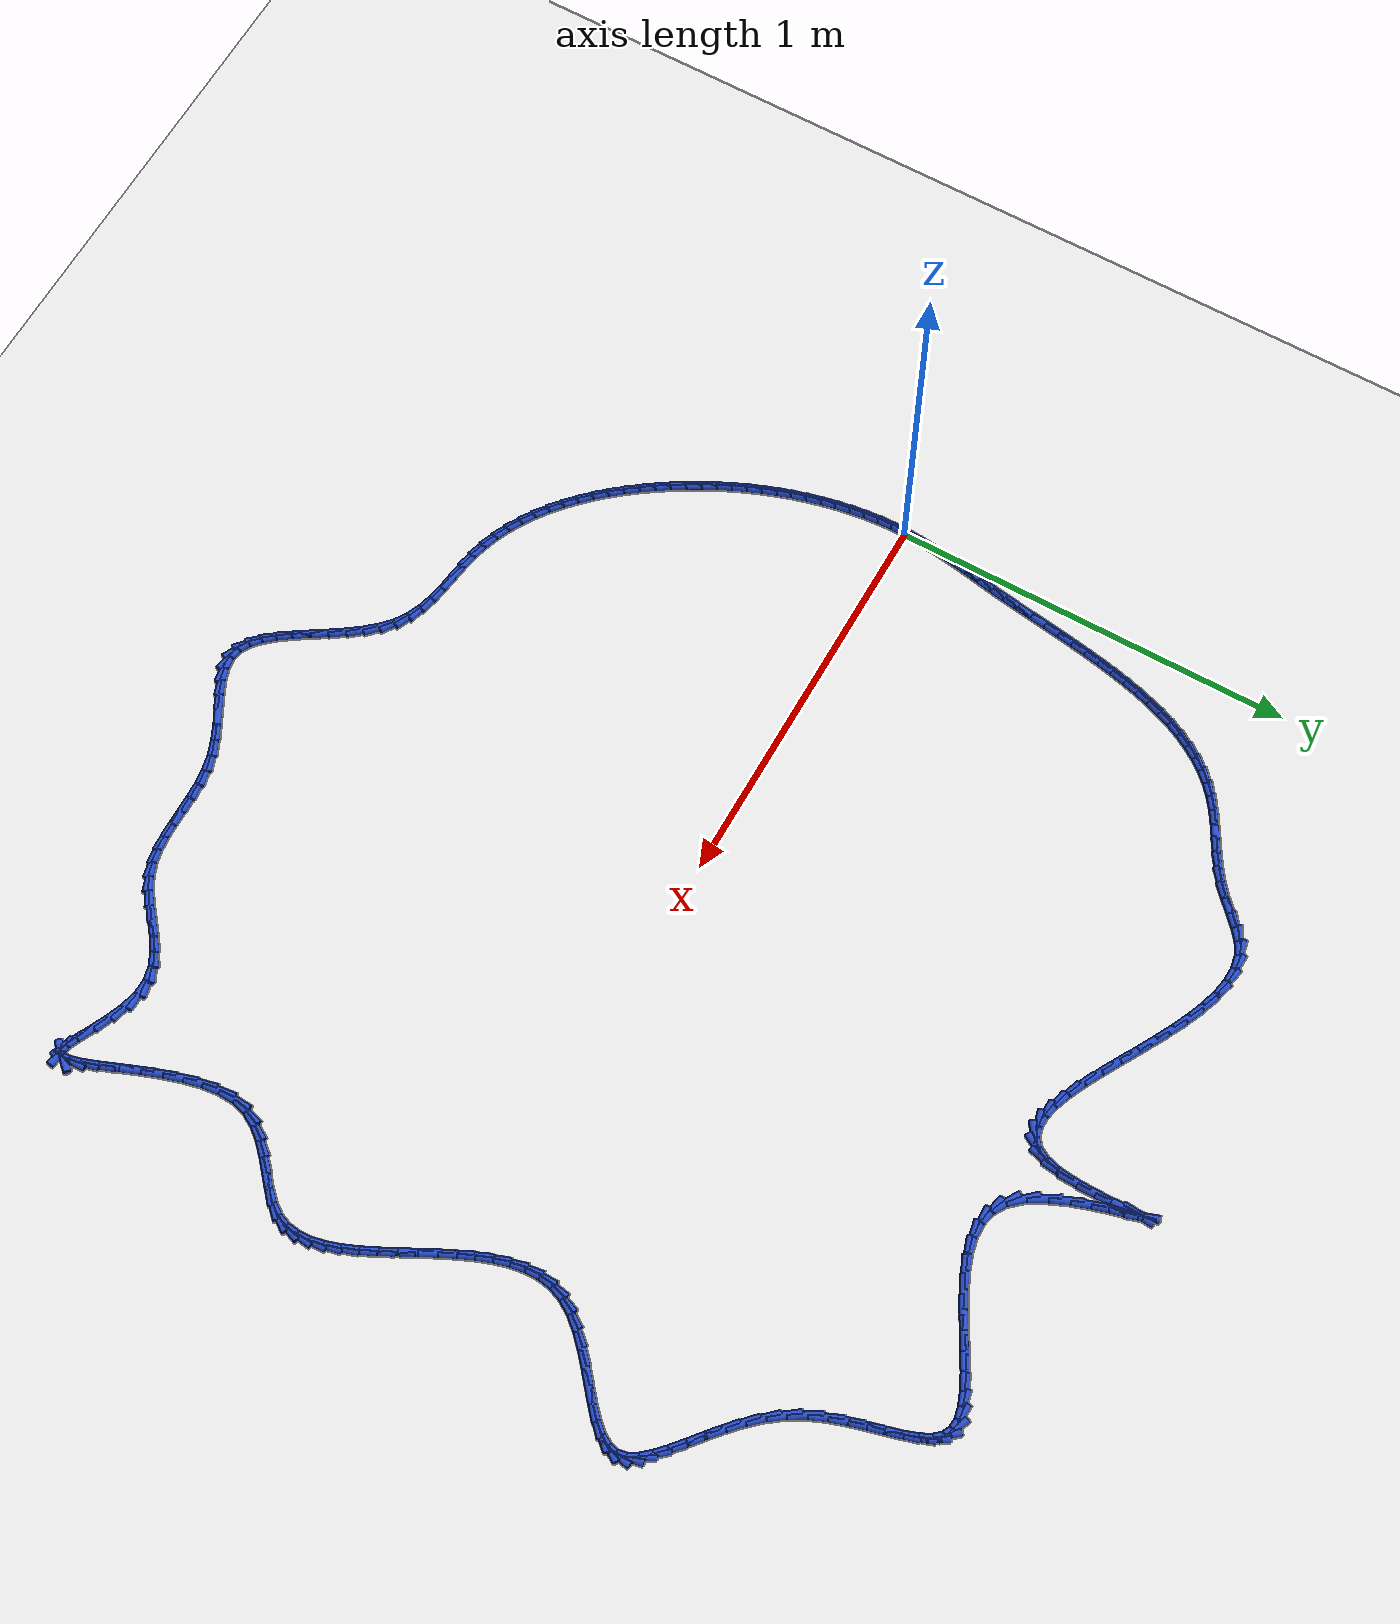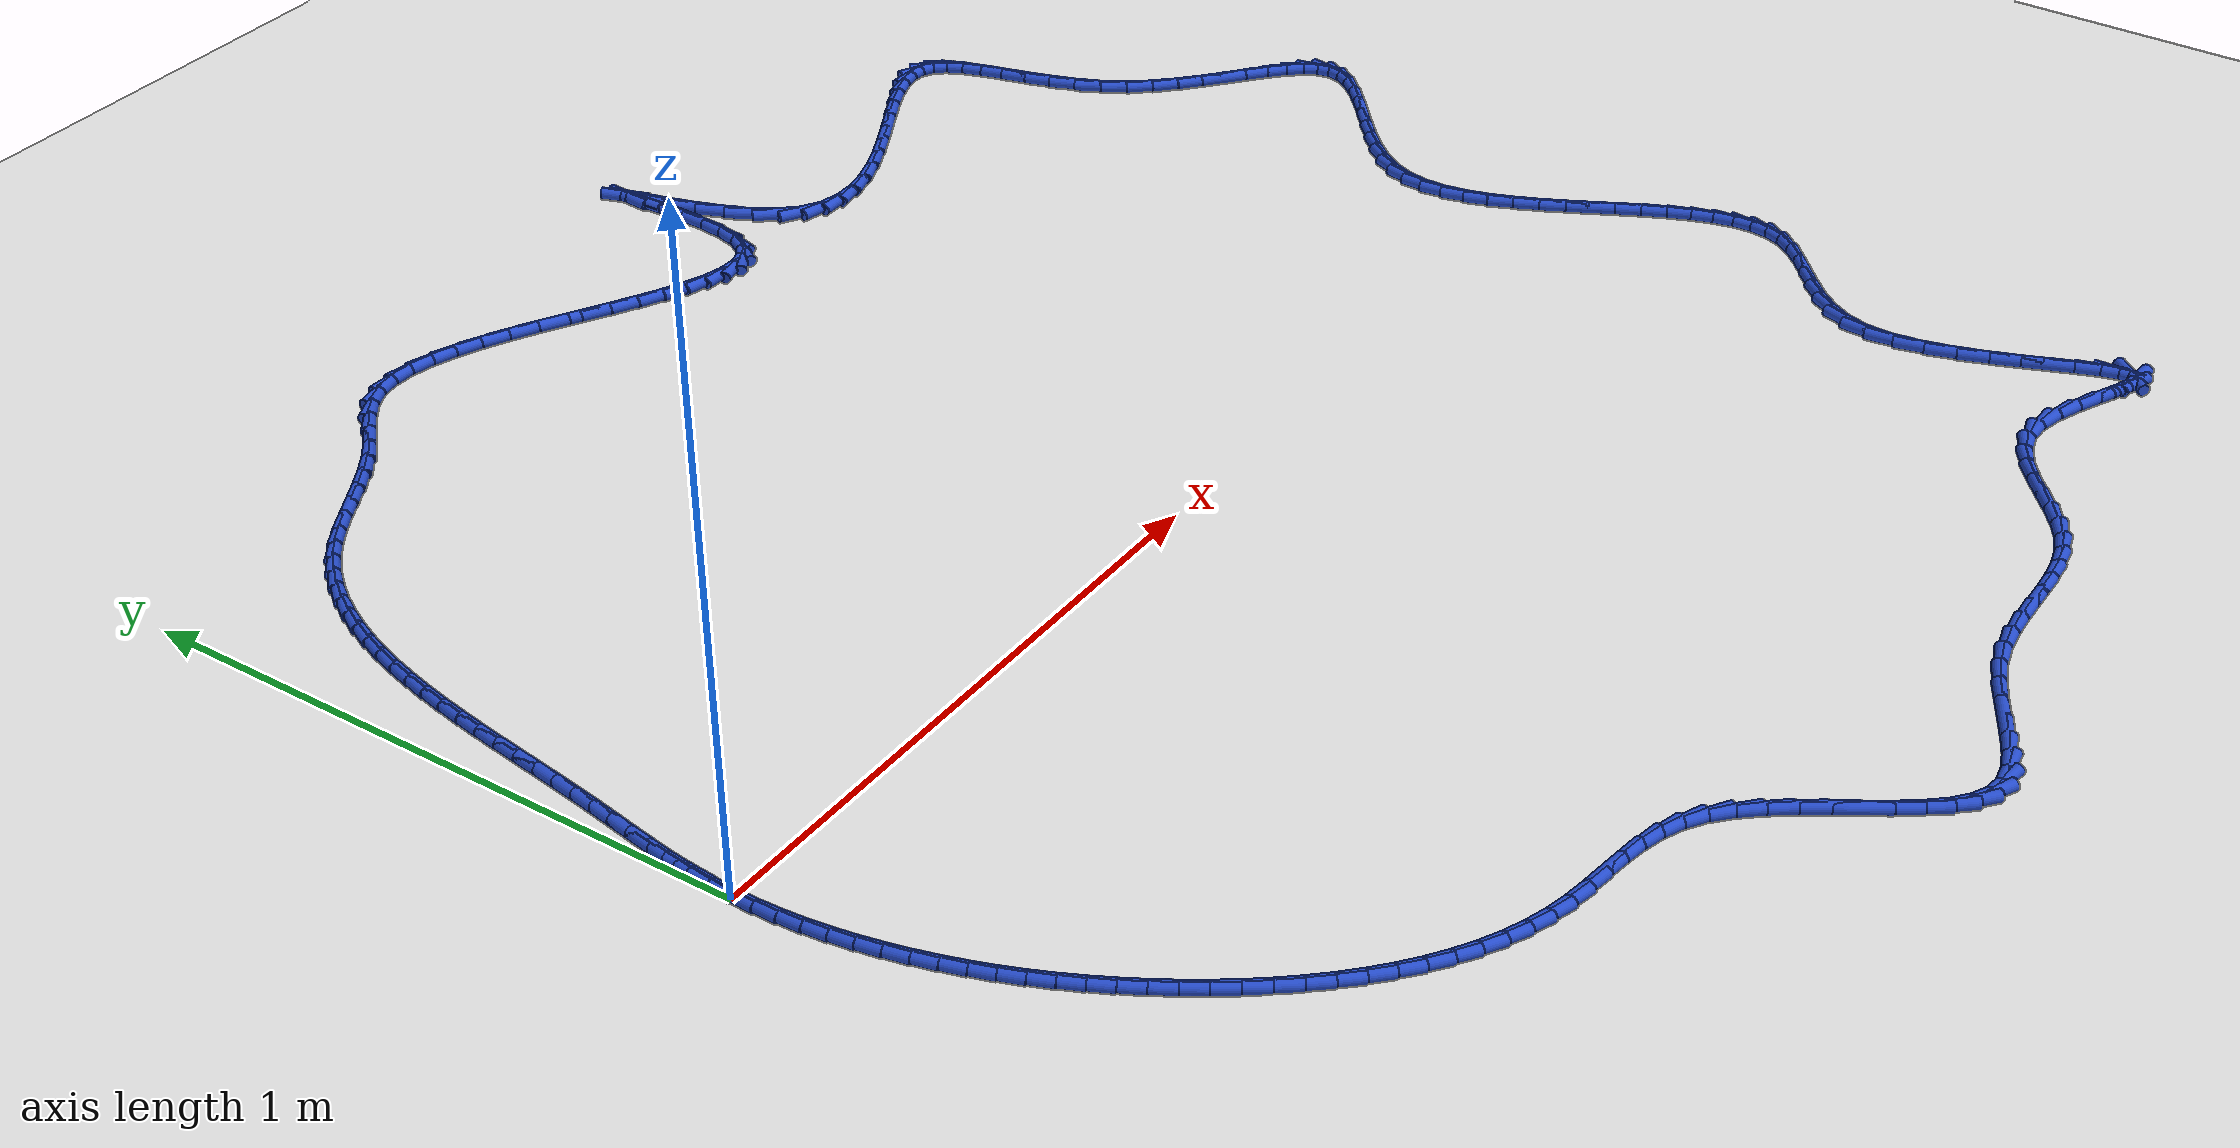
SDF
<sdf version="1.6">
 <world name="default">
  <light name="sun" type="directional">
   <pose>0 0 10 0 -0 0</pose>
   <diffuse>0.8 0.8 0.8 1</diffuse>
   <specular>0.2 0.2 0.2 1</specular>
   <attenuation>
    <range>1000</range>
    <constant>0.9</constant>
    <linear>0.01</linear>
    <quadratic>0.001</quadratic>
   </attenuation>
   <direction>-0.5 0.1 -0.9</direction>
  </light>
  <model name="ground_plane">
   <static>1</static>
   <link name="link">
    <collision name="collision">
     <geometry><plane><normal>0 0 1</normal><size>100 100</size></plane></geometry>
     <surface><friction><ode><mu>100</mu><mu2>50</mu2></ode></friction></surface>
    </collision>
    <visual name="visual">
     <cast_shadows>0</cast_shadows>
     <geometry><plane><normal>0 0 1</normal><size>100 100</size></plane></geometry>
     <material>
      <script><uri>file://media/materials/scripts/gazebo.material</uri><name>Gazebo/WhiteGlow</name></script>
     </material>
    </visual>
   </link>
  </model>
  <gravity>0 0 -9.8</gravity>
  <magnetic_field>6e-06 2.3e-05 -4.2e-05</magnetic_field>
  <atmosphere type="adiabatic"/>
  <physics name="default_physics" default="0" type="ode">
   <max_step_size>0.001</max_step_size>
   <real_time_factor>1</real_time_factor>
   <real_time_update_rate>1000</real_time_update_rate>
  </physics>
  <scene><ambient>0.4 0.4 0.4 1</ambient><background>0.7 0.7 0.7 1</background><shadows>1</shadows></scene>
  <spherical_coordinates>
   <surface_model>EARTH_WGS84</surface_model>
   <latitude_deg>0</latitude_deg>
   <longitude_deg>0</longitude_deg>
   <elevation>0</elevation>
   <heading_deg>0</heading_deg>
  </spherical_coordinates>
  <model name="line">
   <link name="link_0">
    <pose>6.938893903907228e-18 -2.0816681711721685e-17 0.01 0 1.57 1.5196126872821865</pose>
    <collision name="collision">
     <geometry><cylinder><radius>0.01</radius><length>0.08</length></cylinder></geometry>
    </collision>
    <visual name="visual">
     <material>
      <script><name>Gazebo/Blue</name><uri>file://media/materials/scripts/gazebo.material</uri></script>
     </material>
     <geometry><cylinder><radius>0.01</radius><length>0.08</length></cylinder></geometry>
    </visual>
   </link>
   <link name="link_1">
    <pose>0.0018341050438170502 0.03580251697795233 0.01 0 1.57 1.4773591040473364</pose>
    <collision name="collision">
     <geometry><cylinder><radius>0.01</radius><length>0.08</length></cylinder></geometry>
    </collision>
    <visual name="visual">
     <material>
      <script><name>Gazebo/Blue</name><uri>file://media/materials/scripts/gazebo.material</uri></script>
     </material>
     <geometry><cylinder><radius>0.01</radius><length>0.08</length></cylinder></geometry>
    </visual>
   </link>
   <link name="link_2">
    <pose>0.005172107383323331 0.07142303761819246 0.01 0 1.57 1.4437243982588635</pose>
    <collision name="collision">
     <geometry><cylinder><radius>0.01</radius><length>0.08</length></cylinder></geometry>
    </collision>
    <visual name="visual">
     <material>
      <script><name>Gazebo/Blue</name><uri>file://media/materials/scripts/gazebo.material</uri></script>
     </material>
     <geometry><cylinder><radius>0.01</radius><length>0.08</length></cylinder></geometry>
    </visual>
   </link>
   <link name="link_3">
    <pose>0.009717413193203276 0.1069998539755503 0.01 0 1.57 1.419020517256803</pose>
    <collision name="collision">
     <geometry><cylinder><radius>0.01</radius><length>0.08</length></cylinder></geometry>
    </collision>
    <visual name="visual">
     <material>
      <script><name>Gazebo/Blue</name><uri>file://media/materials/scripts/gazebo.material</uri></script>
     </material>
     <geometry><cylinder><radius>0.01</radius><length>0.08</length></cylinder></geometry>
    </visual>
   </link>
   <link name="link_4">
    <pose>0.015173428648141281 0.14267125810485565 0.01 0 1.57 1.403315764648538</pose>
    <collision name="collision">
     <geometry><cylinder><radius>0.01</radius><length>0.08</length></cylinder></geometry>
    </collision>
    <visual name="visual">
     <material>
      <script><name>Gazebo/Blue</name><uri>file://media/materials/scripts/gazebo.material</uri></script>
     </material>
     <geometry><cylinder><radius>0.01</radius><length>0.08</length></cylinder></geometry>
    </visual>
   </link>
   <link name="link_5">
    <pose>0.021243559922821783 0.17857554206093854 0.01 0 1.57 1.3964956989461528</pose>
    <collision name="collision">
     <geometry><cylinder><radius>0.01</radius><length>0.08</length></cylinder></geometry>
    </collision>
    <visual name="visual">
     <material>
      <script><name>Gazebo/Blue</name><uri>file://media/materials/scripts/gazebo.material</uri></script>
     </material>
     <geometry><cylinder><radius>0.01</radius><length>0.08</length></cylinder></geometry>
    </visual>
   </link>
   <link name="link_6">
    <pose>0.027631213191929193 0.21485099789862874 0.01 0 1.57 1.3983098857076652</pose>
    <collision name="collision">
     <geometry><cylinder><radius>0.01</radius><length>0.08</length></cylinder></geometry>
    </collision>
    <visual name="visual">
     <material>
      <script><name>Gazebo/Blue</name><uri>file://media/materials/scripts/gazebo.material</uri></script>
     </material>
     <geometry><cylinder><radius>0.01</radius><length>0.08</length></cylinder></geometry>
    </visual>
   </link>
   <link name="link_7">
    <pose>0.03403979463014792 0.25163591767275617 0.01 0 1.57 1.4081093619255767</pose>
    <collision name="collision">
     <geometry><cylinder><radius>0.01</radius><length>0.08</length></cylinder></geometry>
    </collision>
    <visual name="visual">
     <material>
      <script><name>Gazebo/Blue</name><uri>file://media/materials/scripts/gazebo.material</uri></script>
     </material>
     <geometry><cylinder><radius>0.01</radius><length>0.08</length></cylinder></geometry>
    </visual>
   </link>
   <link name="link_8">
    <pose>0.04018281333392843 0.2890619461315127 0.01 0 1.57 1.419282910490159</pose>
    <collision name="collision">
     <geometry><cylinder><radius>0.01</radius><length>0.08</length></cylinder></geometry>
    </collision>
    <visual name="visual">
     <material>
      <script><name>Gazebo/Blue</name><uri>file://media/materials/scripts/gazebo.material</uri></script>
     </material>
     <geometry><cylinder><radius>0.01</radius><length>0.08</length></cylinder></geometry>
    </visual>
   </link>
   <link name="link_9">
    <pose>0.045993105781639884 0.327116419634341 0.01 0 1.57 1.4258902677619953</pose>
    <collision name="collision">
     <geometry><cylinder><radius>0.01</radius><length>0.08</length></cylinder></geometry>
    </collision>
    <visual name="visual">
     <material>
      <script><name>Gazebo/Blue</name><uri>file://media/materials/scripts/gazebo.material</uri></script>
     </material>
     <geometry><cylinder><radius>0.01</radius><length>0.08</length></cylinder></geometry>
    </visual>
   </link>
   <link name="link_10">
    <pose>0.05161582714931033 0.365646977577666 0.01 0 1.57 1.427910235961586</pose>
    <collision name="collision">
     <geometry><cylinder><radius>0.01</radius><length>0.08</length></cylinder></geometry>
    </collision>
    <visual name="visual">
     <material>
      <script><name>Gazebo/Blue</name><uri>file://media/materials/scripts/gazebo.material</uri></script>
     </material>
     <geometry><cylinder><radius>0.01</radius><length>0.08</length></cylinder></geometry>
    </visual>
   </link>
   <link name="link_11">
    <pose>0.05720483333438501 0.40449553464138405 0.01 0 1.57 1.425471503671163</pose>
    <collision name="collision">
     <geometry><cylinder><radius>0.01</radius><length>0.08</length></cylinder></geometry>
    </collision>
    <visual name="visual">
     <material>
      <script><name>Gazebo/Blue</name><uri>file://media/materials/scripts/gazebo.material</uri></script>
     </material>
     <geometry><cylinder><radius>0.01</radius><length>0.08</length></cylinder></geometry>
    </visual>
   </link>
   <link name="link_12">
    <pose>0.06291398023430894 0.4435040055053905 0.01 0 1.57 1.4186088225762155</pose>
    <collision name="collision">
     <geometry><cylinder><radius>0.01</radius><length>0.08</length></cylinder></geometry>
    </collision>
    <visual name="visual">
     <material>
      <script><name>Gazebo/Blue</name><uri>file://media/materials/scripts/gazebo.material</uri></script>
     </material>
     <geometry><cylinder><radius>0.01</radius><length>0.08</length></cylinder></geometry>
    </visual>
   </link>
   <link name="link_13">
    <pose>0.06889712374652725 0.4825143048495812 0.01 0 1.57 1.4072677283929116</pose>
    <collision name="collision">
     <geometry><cylinder><radius>0.01</radius><length>0.08</length></cylinder></geometry>
    </collision>
    <visual name="visual">
     <material>
      <script><name>Gazebo/Blue</name><uri>file://media/materials/scripts/gazebo.material</uri></script>
     </material>
     <geometry><cylinder><radius>0.01</radius><length>0.08</length></cylinder></geometry>
    </visual>
   </link>
   <link name="link_14">
    <pose>0.07530811976848513 0.5213683473538522 0.01 0 1.57 1.3913073940252811</pose>
    <collision name="collision">
     <geometry><cylinder><radius>0.01</radius><length>0.08</length></cylinder></geometry>
    </collision>
    <visual name="visual">
     <material>
      <script><name>Gazebo/Blue</name><uri>file://media/materials/scripts/gazebo.material</uri></script>
     </material>
     <geometry><cylinder><radius>0.01</radius><length>0.08</length></cylinder></geometry>
    </visual>
   </link>
   <link name="link_15">
    <pose>0.08230082419762767 0.5599080476980991 0.01 0 1.57 1.370502373686411</pose>
    <collision name="collision">
     <geometry><cylinder><radius>0.01</radius><length>0.08</length></cylinder></geometry>
    </collision>
    <visual name="visual">
     <material>
      <script><name>Gazebo/Blue</name><uri>file://media/materials/scripts/gazebo.material</uri></script>
     </material>
     <geometry><cylinder><radius>0.01</radius><length>0.08</length></cylinder></geometry>
    </visual>
   </link>
   <link name="link_16">
    <pose>0.09002909293139999 0.5979753205622179 0.01 0 1.57 1.3445444193676876</pose>
    <collision name="collision">
     <geometry><cylinder><radius>0.01</radius><length>0.08</length></cylinder></geometry>
    </collision>
    <visual name="visual">
     <material>
      <script><name>Gazebo/Blue</name><uri>file://media/materials/scripts/gazebo.material</uri></script>
     </material>
     <geometry><cylinder><radius>0.01</radius><length>0.08</length></cylinder></geometry>
    </visual>
   </link>
   <link name="link_17">
    <pose>0.0986467818672472 0.6354120806261041 0.01 0 1.57 1.3130461849527493</pose>
    <collision name="collision">
     <geometry><cylinder><radius>0.01</radius><length>0.08</length></cylinder></geometry>
    </collision>
    <visual name="visual">
     <material>
      <script><name>Gazebo/Blue</name><uri>file://media/materials/scripts/gazebo.material</uri></script>
     </material>
     <geometry><cylinder><radius>0.01</radius><length>0.08</length></cylinder></geometry>
    </visual>
   </link>
   <link name="link_18">
    <pose>0.10830774690261441 0.6720602425696538 0.01 0 1.57 1.2755495704446145</pose>
    <collision name="collision">
     <geometry><cylinder><radius>0.01</radius><length>0.08</length></cylinder></geometry>
    </collision>
    <visual name="visual">
     <material>
      <script><name>Gazebo/Blue</name><uri>file://media/materials/scripts/gazebo.material</uri></script>
     </material>
     <geometry><cylinder><radius>0.01</radius><length>0.08</length></cylinder></geometry>
    </visual>
   </link>
   <link name="link_19">
    <pose>0.11916584393494674 0.7077617210727625 0.01 0 1.57 1.2315427428161414</pose>
    <collision name="collision">
     <geometry><cylinder><radius>0.01</radius><length>0.08</length></cylinder></geometry>
    </collision>
    <visual name="visual">
     <material>
      <script><name>Gazebo/Blue</name><uri>file://media/materials/scripts/gazebo.material</uri></script>
     </material>
     <geometry><cylinder><radius>0.01</radius><length>0.08</length></cylinder></geometry>
    </visual>
   </link>
   <link name="link_20">
    <pose>0.1313749288616894 0.7423584308153264 0.01 0 1.57 1.1804913949938178</pose>
    <collision name="collision">
     <geometry><cylinder><radius>0.01</radius><length>0.08</length></cylinder></geometry>
    </collision>
    <visual name="visual">
     <material>
      <script><name>Gazebo/Blue</name><uri>file://media/materials/scripts/gazebo.material</uri></script>
     </material>
     <geometry><cylinder><radius>0.01</radius><length>0.08</length></cylinder></geometry>
    </visual>
   </link>
   <link name="link_21">
    <pose>0.14508885758028742 0.7756922864772411 0.01 0 1.57 1.1218911109934948</pose>
    <collision name="collision">
     <geometry><cylinder><radius>0.01</radius><length>0.08</length></cylinder></geometry>
    </collision>
    <visual name="visual">
     <material>
      <script><name>Gazebo/Blue</name><uri>file://media/materials/scripts/gazebo.material</uri></script>
     </material>
     <geometry><cylinder><radius>0.01</radius><length>0.08</length></cylinder></geometry>
    </visual>
   </link>
   <link name="link_22">
    <pose>0.160461485988186 0.8076052027384023 0.01 0 1.57 1.0553476685875287</pose>
    <collision name="collision">
     <geometry><cylinder><radius>0.01</radius><length>0.08</length></cylinder></geometry>
    </collision>
    <visual name="visual">
     <material>
      <script><name>Gazebo/Blue</name><uri>file://media/materials/scripts/gazebo.material</uri></script>
     </material>
     <geometry><cylinder><radius>0.01</radius><length>0.08</length></cylinder></geometry>
    </visual>
   </link>
   <link name="link_23">
    <pose>0.17764666998283013 0.8379390942787058 0.01 0 1.57 0.9806886736086488</pose>
    <collision name="collision">
     <geometry><cylinder><radius>0.01</radius><length>0.08</length></cylinder></geometry>
    </collision>
    <visual name="visual">
     <material>
      <script><name>Gazebo/Blue</name><uri>file://media/materials/scripts/gazebo.material</uri></script>
     </material>
     <geometry><cylinder><radius>0.01</radius><length>0.08</length></cylinder></geometry>
    </visual>
   </link>
   <link name="link_24">
    <pose>0.19679826546166507 0.8665358757780477 0.01 0 1.57 0.898100394046</pose>
    <collision name="collision">
     <geometry><cylinder><radius>0.01</radius><length>0.08</length></cylinder></geometry>
    </collision>
    <visual name="visual">
     <material>
      <script><name>Gazebo/Blue</name><uri>file://media/materials/scripts/gazebo.material</uri></script>
     </material>
     <geometry><cylinder><radius>0.01</radius><length>0.08</length></cylinder></geometry>
    </visual>
   </link>
   <link name="link_25">
    <pose>0.21807012832213565 0.893237461916323 0.01 0 1.57 0.8082665803071494</pose>
    <collision name="collision">
     <geometry><cylinder><radius>0.01</radius><length>0.08</length></cylinder></geometry>
    </collision>
    <visual name="visual">
     <material>
      <script><name>Gazebo/Blue</name><uri>file://media/materials/scripts/gazebo.material</uri></script>
     </material>
     <geometry><cylinder><radius>0.01</radius><length>0.08</length></cylinder></geometry>
    </visual>
   </link>
   <link name="link_26">
    <pose>0.24161611446168746 0.9178857673734286 0.01 0 1.57 0.7124696456041776</pose>
    <collision name="collision">
     <geometry><cylinder><radius>0.01</radius><length>0.08</length></cylinder></geometry>
    </collision>
    <visual name="visual">
     <material>
      <script><name>Gazebo/Blue</name><uri>file://media/materials/scripts/gazebo.material</uri></script>
     </material>
     <geometry><cylinder><radius>0.01</radius><length>0.08</length></cylinder></geometry>
    </visual>
   </link>
   <link name="link_27">
    <pose>0.26758998024599756 0.9403228238718759 0.01 0 1.57 0.6205473133203346</pose>
    <collision name="collision">
     <geometry><cylinder><radius>0.01</radius><length>0.08</length></cylinder></geometry>
    </collision>
    <visual name="visual">
     <material>
      <script><name>Gazebo/Blue</name><uri>file://media/materials/scripts/gazebo.material</uri></script>
     </material>
     <geometry><cylinder><radius>0.01</radius><length>0.08</length></cylinder></geometry>
    </visual>
   </link>
   <link name="link_28">
    <pose>0.29596470244814815 0.960603247687919 0.01 0 1.57 0.5576238310340662</pose>
    <collision name="collision">
     <geometry><cylinder><radius>0.01</radius><length>0.08</length></cylinder></geometry>
    </collision>
    <visual name="visual">
     <material>
      <script><name>Gazebo/Blue</name><uri>file://media/materials/scripts/gazebo.material</uri></script>
     </material>
     <geometry><cylinder><radius>0.01</radius><length>0.08</length></cylinder></geometry>
    </visual>
   </link>
   <link name="link_29">
    <pose>0.3261588198050851 0.9794336366671805 0.01 0 1.57 0.5265953932676376</pose>
    <collision name="collision">
     <geometry><cylinder><radius>0.01</radius><length>0.08</length></cylinder></geometry>
    </collision>
    <visual name="visual">
     <material>
      <script><name>Gazebo/Blue</name><uri>file://media/materials/scripts/gazebo.material</uri></script>
     </material>
     <geometry><cylinder><radius>0.01</radius><length>0.08</length></cylinder></geometry>
    </visual>
   </link>
   <link name="link_30">
    <pose>0.3574849373258601 0.997645159542667 0.01 0 1.57 0.5255085717485836</pose>
    <collision name="collision">
     <geometry><cylinder><radius>0.01</radius><length>0.08</length></cylinder></geometry>
    </collision>
    <visual name="visual">
     <material>
      <script><name>Gazebo/Blue</name><uri>file://media/materials/scripts/gazebo.material</uri></script>
     </material>
     <geometry><cylinder><radius>0.01</radius><length>0.08</length></cylinder></geometry>
    </visual>
   </link>
   <link name="link_31">
    <pose>0.3892556600195249 1.0160689850473856 0.01 0 1.57 0.5531602748926076</pose>
    <collision name="collision">
     <geometry><cylinder><radius>0.01</radius><length>0.08</length></cylinder></geometry>
    </collision>
    <visual name="visual">
     <material>
      <script><name>Gazebo/Blue</name><uri>file://media/materials/scripts/gazebo.material</uri></script>
     </material>
     <geometry><cylinder><radius>0.01</radius><length>0.08</length></cylinder></geometry>
    </visual>
   </link>
   <link name="link_32">
    <pose>0.420783592895131 1.0355362819143434 0.01 0 1.57 0.6090463096490613</pose>
    <collision name="collision">
     <geometry><cylinder><radius>0.01</radius><length>0.08</length></cylinder></geometry>
    </collision>
    <visual name="visual">
     <material>
      <script><name>Gazebo/Blue</name><uri>file://media/materials/scripts/gazebo.material</uri></script>
     </material>
     <geometry><cylinder><radius>0.01</radius><length>0.08</length></cylinder></geometry>
    </visual>
   </link>
   <link name="link_33">
    <pose>0.4513813409617303 1.0568782188765482 0.01 0 1.57 0.6923891893803408</pose>
    <collision name="collision">
     <geometry><cylinder><radius>0.01</radius><length>0.08</length></cylinder></geometry>
    </collision>
    <visual name="visual">
     <material>
      <script><name>Gazebo/Blue</name><uri>file://media/materials/scripts/gazebo.material</uri></script>
     </material>
     <geometry><cylinder><radius>0.01</radius><length>0.08</length></cylinder></geometry>
    </visual>
   </link>
   <link name="link_34">
    <pose>0.480366219760524 1.0809171384096203 0.01 0 1.57 0.7667306337546183</pose>
    <collision name="collision">
     <geometry><cylinder><radius>0.01</radius><length>0.08</length></cylinder></geometry>
    </collision>
    <visual name="visual">
     <material>
      <script><name>Gazebo/Blue</name><uri>file://media/materials/scripts/gazebo.material</uri></script>
     </material>
     <geometry><cylinder><radius>0.01</radius><length>0.08</length></cylinder></geometry>
    </visual>
   </link>
   <link name="link_35">
    <pose>0.5077066447885126 1.1072553985774676 0.01 0 1.57 0.7628272210278371</pose>
    <collision name="collision">
     <geometry><cylinder><radius>0.01</radius><length>0.08</length></cylinder></geometry>
    </collision>
    <visual name="visual">
     <material>
      <script><name>Gazebo/Blue</name><uri>file://media/materials/scripts/gazebo.material</uri></script>
     </material>
     <geometry><cylinder><radius>0.01</radius><length>0.08</length></cylinder></geometry>
    </visual>
   </link>
   <link name="link_36">
    <pose>0.534681732381642 1.1330394601924367 0.01 0 1.57 0.6669708569229804</pose>
    <collision name="collision">
     <geometry><cylinder><radius>0.01</radius><length>0.08</length></cylinder></geometry>
    </collision>
    <visual name="visual">
     <material>
      <script><name>Gazebo/Blue</name><uri>file://media/materials/scripts/gazebo.material</uri></script>
     </material>
     <geometry><cylinder><radius>0.01</radius><length>0.08</length></cylinder></geometry>
    </visual>
   </link>
   <link name="link_37">
    <pose>0.5627278399127258 1.155121157086561 0.01 0 1.57 0.4628962566847399</pose>
    <collision name="collision">
     <geometry><cylinder><radius>0.01</radius><length>0.08</length></cylinder></geometry>
    </collision>
    <visual name="visual">
     <material>
      <script><name>Gazebo/Blue</name><uri>file://media/materials/scripts/gazebo.material</uri></script>
     </material>
     <geometry><cylinder><radius>0.01</radius><length>0.08</length></cylinder></geometry>
    </visual>
   </link>
   <link name="link_38">
    <pose>0.5932750543251479 1.1703660854109748 0.01 0 1.57 0.1945143391421146</pose>
    <collision name="collision">
     <geometry><cylinder><radius>0.01</radius><length>0.08</length></cylinder></geometry>
    </collision>
    <visual name="visual">
     <material>
      <script><name>Gazebo/Blue</name><uri>file://media/materials/scripts/gazebo.material</uri></script>
     </material>
     <geometry><cylinder><radius>0.01</radius><length>0.08</length></cylinder></geometry>
    </visual>
   </link>
   <link name="link_39">
    <pose>0.6271185139508031 1.1770334245638254 0.01 0 1.57 -0.02935698226489924</pose>
    <collision name="collision">
     <geometry><cylinder><radius>0.01</radius><length>0.08</length></cylinder></geometry>
    </collision>
    <visual name="visual">
     <material>
      <script><name>Gazebo/Blue</name><uri>file://media/materials/scripts/gazebo.material</uri></script>
     </material>
     <geometry><cylinder><radius>0.01</radius><length>0.08</length></cylinder></geometry>
    </visual>
   </link>
   <link name="link_40">
    <pose>0.6638817208534781 1.1759538575976964 0.01 0 1.57 -0.19450644139646786</pose>
    <collision name="collision">
     <geometry><cylinder><radius>0.01</radius><length>0.08</length></cylinder></geometry>
    </collision>
    <visual name="visual">
     <material>
      <script><name>Gazebo/Blue</name><uri>file://media/materials/scripts/gazebo.material</uri></script>
     </material>
     <geometry><cylinder><radius>0.01</radius><length>0.08</length></cylinder></geometry>
    </visual>
   </link>
   <link name="link_41">
    <pose>0.7030617708628657 1.1682355035764718 0.01 0 1.57 -0.31188554700091176</pose>
    <collision name="collision">
     <geometry><cylinder><radius>0.01</radius><length>0.08</length></cylinder></geometry>
    </collision>
    <visual name="visual">
     <material>
      <script><name>Gazebo/Blue</name><uri>file://media/materials/scripts/gazebo.material</uri></script>
     </material>
     <geometry><cylinder><radius>0.01</radius><length>0.08</length></cylinder></geometry>
    </visual>
   </link>
   <link name="link_42">
    <pose>0.7441557598086586 1.1549864815640345 0.01 0 1.57 -0.3940119534991859</pose>
    <collision name="collision">
     <geometry><cylinder><radius>0.01</radius><length>0.08</length></cylinder></geometry>
    </collision>
    <visual name="visual">
     <material>
      <script><name>Gazebo/Blue</name><uri>file://media/materials/scripts/gazebo.material</uri></script>
     </material>
     <geometry><cylinder><radius>0.01</radius><length>0.08</length></cylinder></geometry>
    </visual>
   </link>
   <link name="link_43">
    <pose>0.7866607835205492 1.1373149106242688 0.01 0 1.57 -0.4502811679912142</pose>
    <collision name="collision">
     <geometry><cylinder><radius>0.01</radius><length>0.08</length></cylinder></geometry>
    </collision>
    <visual name="visual">
     <material>
      <script><name>Gazebo/Blue</name><uri>file://media/materials/scripts/gazebo.material</uri></script>
     </material>
     <geometry><cylinder><radius>0.01</radius><length>0.08</length></cylinder></geometry>
    </visual>
   </link>
   <link name="link_44">
    <pose>0.8300739378282304 1.1163289098210578 0.01 0 1.57 -0.486798429600046</pose>
    <collision name="collision">
     <geometry><cylinder><radius>0.01</radius><length>0.08</length></cylinder></geometry>
    </collision>
    <visual name="visual">
     <material>
      <script><name>Gazebo/Blue</name><uri>file://media/materials/scripts/gazebo.material</uri></script>
     </material>
     <geometry><cylinder><radius>0.01</radius><length>0.08</length></cylinder></geometry>
    </visual>
   </link>
   <link name="link_45">
    <pose>0.8738923185613948 1.0931365982182857 0.01 0 1.57 -0.5071198954846758</pose>
    <collision name="collision">
     <geometry><cylinder><radius>0.01</radius><length>0.08</length></cylinder></geometry>
    </collision>
    <visual name="visual">
     <material>
      <script><name>Gazebo/Blue</name><uri>file://media/materials/scripts/gazebo.material</uri></script>
     </material>
     <geometry><cylinder><radius>0.01</radius><length>0.08</length></cylinder></geometry>
    </visual>
   </link>
   <link name="link_46">
    <pose>0.9176130215497348 1.0688460948798353 0.01 0 1.57 -0.5128387175850626</pose>
    <collision name="collision">
     <geometry><cylinder><radius>0.01</radius><length>0.08</length></cylinder></geometry>
    </collision>
    <visual name="visual">
     <material>
      <script><name>Gazebo/Blue</name><uri>file://media/materials/scripts/gazebo.material</uri></script>
     </material>
     <geometry><cylinder><radius>0.01</radius><length>0.08</length></cylinder></geometry>
    </visual>
   </link>
   <link name="link_47">
    <pose>0.9607331426229436 1.0445655188695913 0.01 0 1.57 -0.5038180873314078</pose>
    <collision name="collision">
     <geometry><cylinder><radius>0.01</radius><length>0.08</length></cylinder></geometry>
    </collision>
    <visual name="visual">
     <material>
      <script><name>Gazebo/Blue</name><uri>file://media/materials/scripts/gazebo.material</uri></script>
     </material>
     <geometry><cylinder><radius>0.01</radius><length>0.08</length></cylinder></geometry>
    </visual>
   </link>
   <link name="link_48">
    <pose>1.0027497776107137 1.021402989251437 0.01 0 1.57 -0.47801895455520976</pose>
    <collision name="collision">
     <geometry><cylinder><radius>0.01</radius><length>0.08</length></cylinder></geometry>
    </collision>
    <visual name="visual">
     <material>
      <script><name>Gazebo/Blue</name><uri>file://media/materials/scripts/gazebo.material</uri></script>
     </material>
     <geometry><cylinder><radius>0.01</radius><length>0.08</length></cylinder></geometry>
    </visual>
   </link>
   <link name="link_49">
    <pose>1.0431600223427369 1.0004666250892553 0.01 0 1.57 -0.4307861925367173</pose>
    <collision name="collision">
     <geometry><cylinder><radius>0.01</radius><length>0.08</length></cylinder></geometry>
    </collision>
    <visual name="visual">
     <material>
      <script><name>Gazebo/Blue</name><uri>file://media/materials/scripts/gazebo.material</uri></script>
     </material>
     <geometry><cylinder><radius>0.01</radius><length>0.08</length></cylinder></geometry>
    </visual>
   </link>
   <link name="link_50">
    <pose>1.0814609726487072 0.9828645454469305 0.01 0 1.57 -0.3532663966977162</pose>
    <collision name="collision">
     <geometry><cylinder><radius>0.01</radius><length>0.08</length></cylinder></geometry>
    </collision>
    <visual name="visual">
     <material>
      <script><name>Gazebo/Blue</name><uri>file://media/materials/scripts/gazebo.material</uri></script>
     </material>
     <geometry><cylinder><radius>0.01</radius><length>0.08</length></cylinder></geometry>
    </visual>
   </link>
   <link name="link_51">
    <pose>1.1171497243583164 0.9697048693883461 0.01 0 1.57 -0.22948333199046386</pose>
    <collision name="collision">
     <geometry><cylinder><radius>0.01</radius><length>0.08</length></cylinder></geometry>
    </collision>
    <visual name="visual">
     <material>
      <script><name>Gazebo/Blue</name><uri>file://media/materials/scripts/gazebo.material</uri></script>
     </material>
     <geometry><cylinder><radius>0.01</radius><length>0.08</length></cylinder></geometry>
    </visual>
   </link>
   <link name="link_52">
    <pose>1.1497233733012577 0.9620957159773857 0.01 0 1.57 -0.0328146930100318</pose>
    <collision name="collision">
     <geometry><cylinder><radius>0.01</radius><length>0.08</length></cylinder></geometry>
    </collision>
    <visual name="visual">
     <material>
      <script><name>Gazebo/Blue</name><uri>file://media/materials/scripts/gazebo.material</uri></script>
     </material>
     <geometry><cylinder><radius>0.01</radius><length>0.08</length></cylinder></geometry>
    </visual>
   </link>
   <link name="link_53">
    <pose>1.1786790153072229 0.9611452042779329 0.01 0 1.57 0.26786818324499573</pose>
    <collision name="collision">
     <geometry><cylinder><radius>0.01</radius><length>0.08</length></cylinder></geometry>
    </collision>
    <visual name="visual">
     <material>
      <script><name>Gazebo/Blue</name><uri>file://media/materials/scripts/gazebo.material</uri></script>
     </material>
     <geometry><cylinder><radius>0.01</radius><length>0.08</length></cylinder></geometry>
    </visual>
   </link>
   <link name="link_54">
    <pose>1.2035137462059056 0.9679614533538716 0.01 0 1.57 0.6601648099261019</pose>
    <collision name="collision">
     <geometry><cylinder><radius>0.01</radius><length>0.08</length></cylinder></geometry>
    </collision>
    <visual name="visual">
     <material>
      <script><name>Gazebo/Blue</name><uri>file://media/materials/scripts/gazebo.material</uri></script>
     </material>
     <geometry><cylinder><radius>0.01</radius><length>0.08</length></cylinder></geometry>
    </visual>
   </link>
   <link name="link_55">
    <pose>1.223724661826998 0.9836525822690851 0.01 0 1.57 1.0396000001866803</pose>
    <collision name="collision">
     <geometry><cylinder><radius>0.01</radius><length>0.08</length></cylinder></geometry>
    </collision>
    <visual name="visual">
     <material>
      <script><name>Gazebo/Blue</name><uri>file://media/materials/scripts/gazebo.material</uri></script>
     </material>
     <geometry><cylinder><radius>0.01</radius><length>0.08</length></cylinder></geometry>
    </visual>
   </link>
   <link name="link_56">
    <pose>1.238808858000193 1.0093267100874572 0.01 0 1.57 1.3131713245645986</pose>
    <collision name="collision">
     <geometry><cylinder><radius>0.01</radius><length>0.08</length></cylinder></geometry>
    </collision>
    <visual name="visual">
     <material>
      <script><name>Gazebo/Blue</name><uri>file://media/materials/scripts/gazebo.material</uri></script>
     </material>
     <geometry><cylinder><radius>0.01</radius><length>0.08</length></cylinder></geometry>
    </visual>
   </link>
   <link name="link_57">
    <pose>1.248387678144507 1.045681718115272 0.01 0 1.57 1.4622001430378122</pose>
    <collision name="collision">
     <geometry><cylinder><radius>0.01</radius><length>0.08</length></cylinder></geometry>
    </collision>
    <visual name="visual">
     <material>
      <script><name>Gazebo/Blue</name><uri>file://media/materials/scripts/gazebo.material</uri></script>
     </material>
     <geometry><cylinder><radius>0.01</radius><length>0.08</length></cylinder></geometry>
    </visual>
   </link>
   <link name="link_58">
    <pose>1.253192331634363 1.0897509584453566 0.01 0 1.57 1.542110129818234</pose>
    <collision name="collision">
     <geometry><cylinder><radius>0.01</radius><length>0.08</length></cylinder></geometry>
    </collision>
    <visual name="visual">
     <material>
      <script><name>Gazebo/Blue</name><uri>file://media/materials/scripts/gazebo.material</uri></script>
     </material>
     <geometry><cylinder><radius>0.01</radius><length>0.08</length></cylinder></geometry>
    </visual>
   </link>
   <link name="link_59">
    <pose>1.254537779484997 1.136640365782208 0.01 0 1.57 -1.5530833813099516</pose>
    <collision name="collision">
     <geometry><cylinder><radius>0.01</radius><length>0.08</length></cylinder></geometry>
    </collision>
    <visual name="visual">
     <material>
      <script><name>Gazebo/Blue</name><uri>file://media/materials/scripts/gazebo.material</uri></script>
     </material>
     <geometry><cylinder><radius>0.01</radius><length>0.08</length></cylinder></geometry>
    </visual>
   </link>
   <link name="link_60">
    <pose>1.2537441861364476 1.1814386942851323 0.01 0 1.57 -1.5281597320739735</pose>
    <collision name="collision">
     <geometry><cylinder><radius>0.01</radius><length>0.08</length></cylinder></geometry>
    </collision>
    <visual name="visual">
     <material>
      <script><name>Gazebo/Blue</name><uri>file://media/materials/scripts/gazebo.material</uri></script>
     </material>
     <geometry><cylinder><radius>0.01</radius><length>0.08</length></cylinder></geometry>
    </visual>
   </link>
   <link name="link_61">
    <pose>1.252131716028752 1.2192346981134374 0.01 0 1.57 -1.5278907593141284</pose>
    <collision name="collision">
     <geometry><cylinder><radius>0.01</radius><length>0.08</length></cylinder></geometry>
    </collision>
    <visual name="visual">
     <material>
      <script><name>Gazebo/Blue</name><uri>file://media/materials/scripts/gazebo.material</uri></script>
     </material>
     <geometry><cylinder><radius>0.01</radius><length>0.08</length></cylinder></geometry>
    </visual>
   </link>
   <link name="link_62">
    <pose>1.2510205336019506 1.2451171314264313 0.01 0 1.57 1.4930545692776775</pose>
    <collision name="collision">
     <geometry><cylinder><radius>0.01</radius><length>0.08</length></cylinder></geometry>
    </collision>
    <visual name="visual">
     <material>
      <script><name>Gazebo/Blue</name><uri>file://media/materials/scripts/gazebo.material</uri></script>
     </material>
     <geometry><cylinder><radius>0.01</radius><length>0.08</length></cylinder></geometry>
    </visual>
   </link>
   <link name="link_63">
    <pose>1.251727871313033 1.2541973498456849 0.01 0 1.57 -1.22918927473231</pose>
    <collision name="collision">
     <geometry><cylinder><radius>0.01</radius><length>0.08</length></cylinder></geometry>
    </collision>
    <visual name="visual">
     <material>
      <script><name>Gazebo/Blue</name><uri>file://media/materials/scripts/gazebo.material</uri></script>
     </material>
     <geometry><cylinder><radius>0.01</radius><length>0.08</length></cylinder></geometry>
    </visual>
   </link>
   <link name="link_64">
    <pose>1.2552029767197268 1.2444233545930647 0.01 0 1.57 -1.3186588763899783</pose>
    <collision name="collision">
     <geometry><cylinder><radius>0.01</radius><length>0.08</length></cylinder></geometry>
    </collision>
    <visual name="visual">
     <material>
      <script><name>Gazebo/Blue</name><uri>file://media/materials/scripts/gazebo.material</uri></script>
     </material>
     <geometry><cylinder><radius>0.01</radius><length>0.08</length></cylinder></geometry>
    </visual>
   </link>
   <link name="link_65">
    <pose>1.2616731956731342 1.2193079929046475 0.01 0 1.57 -1.3120054697427095</pose>
    <collision name="collision">
     <geometry><cylinder><radius>0.01</radius><length>0.08</length></cylinder></geometry>
    </collision>
    <visual name="visual">
     <material>
      <script><name>Gazebo/Blue</name><uri>file://media/materials/scripts/gazebo.material</uri></script>
     </material>
     <geometry><cylinder><radius>0.01</radius><length>0.08</length></cylinder></geometry>
    </visual>
   </link>
   <link name="link_66">
    <pose>1.271281915480273 1.1830113142119165 0.01 0 1.57 -1.2815600569305294</pose>
    <collision name="collision">
     <geometry><cylinder><radius>0.01</radius><length>0.08</length></cylinder></geometry>
    </collision>
    <visual name="visual">
     <material>
      <script><name>Gazebo/Blue</name><uri>file://media/materials/scripts/gazebo.material</uri></script>
     </material>
     <geometry><cylinder><radius>0.01</radius><length>0.08</length></cylinder></geometry>
    </visual>
   </link>
   <link name="link_67">
    <pose>1.284172523448162 1.1396933679463568 0.01 0 1.57 -1.2311695655271155</pose>
    <collision name="collision">
     <geometry><cylinder><radius>0.01</radius><length>0.08</length></cylinder></geometry>
    </collision>
    <visual name="visual">
     <material>
      <script><name>Gazebo/Blue</name><uri>file://media/materials/scripts/gazebo.material</uri></script>
     </material>
     <geometry><cylinder><radius>0.01</radius><length>0.08</length></cylinder></geometry>
    </visual>
   </link>
   <link name="link_68">
    <pose>1.3004884068838212 1.0935142035394507 0.01 0 1.57 -1.1537311726404609</pose>
    <collision name="collision">
     <geometry><cylinder><radius>0.01</radius><length>0.08</length></cylinder></geometry>
    </collision>
    <visual name="visual">
     <material>
      <script><name>Gazebo/Blue</name><uri>file://media/materials/scripts/gazebo.material</uri></script>
     </material>
     <geometry><cylinder><radius>0.01</radius><length>0.08</length></cylinder></geometry>
    </visual>
   </link>
   <link name="link_69">
    <pose>1.320372953094267 1.048633870422683 0.01 0 1.57 -1.031427139022374</pose>
    <collision name="collision">
     <geometry><cylinder><radius>0.01</radius><length>0.08</length></cylinder></geometry>
    </collision>
    <visual name="visual">
     <material>
      <script><name>Gazebo/Blue</name><uri>file://media/materials/scripts/gazebo.material</uri></script>
     </material>
     <geometry><cylinder><radius>0.01</radius><length>0.08</length></cylinder></geometry>
    </visual>
   </link>
   <link name="link_70">
    <pose>1.3439695493865202 1.009212418027537 0.01 0 1.57 -0.827272555788181</pose>
    <collision name="collision">
     <geometry><cylinder><radius>0.01</radius><length>0.08</length></cylinder></geometry>
    </collision>
    <visual name="visual">
     <material>
      <script><name>Gazebo/Blue</name><uri>file://media/materials/scripts/gazebo.material</uri></script>
     </material>
     <geometry><cylinder><radius>0.01</radius><length>0.08</length></cylinder></geometry>
    </visual>
   </link>
   <link name="link_71">
    <pose>1.3714157647301493 0.9793656923565282 0.01 0 1.57 -0.5324765011167155</pose>
    <collision name="collision">
     <geometry><cylinder><radius>0.01</radius><length>0.08</length></cylinder></geometry>
    </collision>
    <visual name="visual">
     <material>
      <script><name>Gazebo/Blue</name><uri>file://media/materials/scripts/gazebo.material</uri></script>
     </material>
     <geometry><cylinder><radius>0.01</radius><length>0.08</length></cylinder></geometry>
    </visual>
   </link>
   <link name="link_72">
    <pose>1.4025601641096337 0.9610139006682872 0.01 0 1.57 -0.2320817622338211</pose>
    <collision name="collision">
     <geometry><cylinder><radius>0.01</radius><length>0.08</length></cylinder></geometry>
    </collision>
    <visual name="visual">
     <material>
      <script><name>Gazebo/Blue</name><uri>file://media/materials/scripts/gazebo.material</uri></script>
     </material>
     <geometry><cylinder><radius>0.01</radius><length>0.08</length></cylinder></geometry>
    </visual>
   </link>
   <link name="link_73">
    <pose>1.4368348671571405 0.9529134061313832 0.01 0 1.57 0.017962697122908416</pose>
    <collision name="collision">
     <geometry><cylinder><radius>0.01</radius><length>0.08</length></cylinder></geometry>
    </collision>
    <visual name="visual">
     <material>
      <script><name>Gazebo/Blue</name><uri>file://media/materials/scripts/gazebo.material</uri></script>
     </material>
     <geometry><cylinder><radius>0.01</radius><length>0.08</length></cylinder></geometry>
    </visual>
   </link>
   <link name="link_74">
    <pose>1.4736396157685836 0.953574589797079 0.01 0 1.57 0.20201681243534686</pose>
    <collision name="collision">
     <geometry><cylinder><radius>0.01</radius><length>0.08</length></cylinder></geometry>
    </collision>
    <visual name="visual">
     <material>
      <script><name>Gazebo/Blue</name><uri>file://media/materials/scripts/gazebo.material</uri></script>
     </material>
     <geometry><cylinder><radius>0.01</radius><length>0.08</length></cylinder></geometry>
    </visual>
   </link>
   <link name="link_75">
    <pose>1.512374151839874 0.9615078327166361 0.01 0 1.57 0.329837909972048</pose>
    <collision name="collision">
     <geometry><cylinder><radius>0.01</radius><length>0.08</length></cylinder></geometry>
    </collision>
    <visual name="visual">
     <material>
      <script><name>Gazebo/Blue</name><uri>file://media/materials/scripts/gazebo.material</uri></script>
     </material>
     <geometry><cylinder><radius>0.01</radius><length>0.08</length></cylinder></geometry>
    </visual>
   </link>
   <link name="link_76">
    <pose>1.552438217266925 0.9752235159413173 0.01 0 1.57 0.41572690695395337</pose>
    <collision name="collision">
     <geometry><cylinder><radius>0.01</radius><length>0.08</length></cylinder></geometry>
    </collision>
    <visual name="visual">
     <material>
      <script><name>Gazebo/Blue</name><uri>file://media/materials/scripts/gazebo.material</uri></script>
     </material>
     <geometry><cylinder><radius>0.01</radius><length>0.08</length></cylinder></geometry>
    </visual>
   </link>
   <link name="link_77">
    <pose>1.59323155394565 0.9932320205223847 0.01 0 1.57 0.47047673224339187</pose>
    <collision name="collision">
     <geometry><cylinder><radius>0.01</radius><length>0.08</length></cylinder></geometry>
    </collision>
    <visual name="visual">
     <material>
      <script><name>Gazebo/Blue</name><uri>file://media/materials/scripts/gazebo.material</uri></script>
     </material>
     <geometry><cylinder><radius>0.01</radius><length>0.08</length></cylinder></geometry>
    </visual>
   </link>
   <link name="link_78">
    <pose>1.6341539037719608 1.0140437275111003 0.01 0 1.57 0.5005091749409764</pose>
    <collision name="collision">
     <geometry><cylinder><radius>0.01</radius><length>0.08</length></cylinder></geometry>
    </collision>
    <visual name="visual">
     <material>
      <script><name>Gazebo/Blue</name><uri>file://media/materials/scripts/gazebo.material</uri></script>
     </material>
     <geometry><cylinder><radius>0.01</radius><length>0.08</length></cylinder></geometry>
    </visual>
   </link>
   <link name="link_79">
    <pose>1.6746050086417705 1.0361690179587266 0.01 0 1.57 0.5084887177179409</pose>
    <collision name="collision">
     <geometry><cylinder><radius>0.01</radius><length>0.08</length></cylinder></geometry>
    </collision>
    <visual name="visual">
     <material>
      <script><name>Gazebo/Blue</name><uri>file://media/materials/scripts/gazebo.material</uri></script>
     </material>
     <geometry><cylinder><radius>0.01</radius><length>0.08</length></cylinder></geometry>
    </visual>
   </link>
   <link name="link_80">
    <pose>1.7139846104509906 1.0581182729165255 0.01 0 1.57 0.49351732082982674</pose>
    <collision name="collision">
     <geometry><cylinder><radius>0.01</radius><length>0.08</length></cylinder></geometry>
    </collision>
    <visual name="visual">
     <material>
      <script><name>Gazebo/Blue</name><uri>file://media/materials/scripts/gazebo.material</uri></script>
     </material>
     <geometry><cylinder><radius>0.01</radius><length>0.08</length></cylinder></geometry>
    </visual>
   </link>
   <link name="link_81">
    <pose>1.7516924510955345 1.0784018734357594 0.01 0 1.57 0.4502487800252181</pose>
    <collision name="collision">
     <geometry><cylinder><radius>0.01</radius><length>0.08</length></cylinder></geometry>
    </collision>
    <visual name="visual">
     <material>
      <script><name>Gazebo/Blue</name><uri>file://media/materials/scripts/gazebo.material</uri></script>
     </material>
     <geometry><cylinder><radius>0.01</radius><length>0.08</length></cylinder></geometry>
    </visual>
   </link>
   <link name="link_82">
    <pose>1.787128272471315 1.0955302005676908 0.01 0 1.57 0.366076407434139</pose>
    <collision name="collision">
     <geometry><cylinder><radius>0.01</radius><length>0.08</length></cylinder></geometry>
    </collision>
    <visual name="visual">
     <material>
      <script><name>Gazebo/Blue</name><uri>file://media/materials/scripts/gazebo.material</uri></script>
     </material>
     <geometry><cylinder><radius>0.01</radius><length>0.08</length></cylinder></geometry>
    </visual>
   </link>
   <link name="link_83">
    <pose>1.8196918164742435 1.1080136353635812 0.01 0 1.57 0.21487427836237946</pose>
    <collision name="collision">
     <geometry><cylinder><radius>0.01</radius><length>0.08</length></cylinder></geometry>
    </collision>
    <visual name="visual">
     <material>
      <script><name>Gazebo/Blue</name><uri>file://media/materials/scripts/gazebo.material</uri></script>
     </material>
     <geometry><cylinder><radius>0.01</radius><length>0.08</length></cylinder></geometry>
    </visual>
   </link>
   <link name="link_84">
    <pose>1.8487828250002334 1.1143625588746935 0.01 0 1.57 -0.05092705816915673</pose>
    <collision name="collision">
     <geometry><cylinder><radius>0.01</radius><length>0.08</length></cylinder></geometry>
    </collision>
    <visual name="visual">
     <material>
      <script><name>Gazebo/Blue</name><uri>file://media/materials/scripts/gazebo.material</uri></script>
     </material>
     <geometry><cylinder><radius>0.01</radius><length>0.08</length></cylinder></geometry>
    </visual>
   </link>
   <link name="link_85">
    <pose>1.873801039945198 1.1130873521522895 0.01 0 1.57 -0.46443987880889465</pose>
    <collision name="collision">
     <geometry><cylinder><radius>0.01</radius><length>0.08</length></cylinder></geometry>
    </collision>
    <visual name="visual">
     <material>
      <script><name>Gazebo/Blue</name><uri>file://media/materials/scripts/gazebo.material</uri></script>
     </material>
     <geometry><cylinder><radius>0.01</radius><length>0.08</length></cylinder></geometry>
    </visual>
   </link>
   <link name="link_86">
    <pose>1.8942353979044115 1.10284992824265 0.01 0 1.57 -0.857843746037428</pose>
    <collision name="collision">
     <geometry><cylinder><radius>0.01</radius><length>0.08</length></cylinder></geometry>
    </collision>
    <visual name="visual">
     <material>
      <script><name>Gazebo/Blue</name><uri>file://media/materials/scripts/gazebo.material</uri></script>
     </material>
     <geometry><cylinder><radius>0.01</radius><length>0.08</length></cylinder></geometry>
    </visual>
   </link>
   <link name="link_87">
    <pose>1.9105546033114136 1.083976718109 0.01 0 1.57 -1.1009814788669952</pose>
    <collision name="collision">
     <geometry><cylinder><radius>0.01</radius><length>0.08</length></cylinder></geometry>
    </collision>
    <visual name="visual">
     <material>
      <script><name>Gazebo/Blue</name><uri>file://media/materials/scripts/gazebo.material</uri></script>
     </material>
     <geometry><cylinder><radius>0.01</radius><length>0.08</length></cylinder></geometry>
    </visual>
   </link>
   <link name="link_88">
    <pose>1.9238333621775472 1.0578236828180854 0.01 0 1.57 -1.2313334530548181</pose>
    <collision name="collision">
     <geometry><cylinder><radius>0.01</radius><length>0.08</length></cylinder></geometry>
    </collision>
    <visual name="visual">
     <material>
      <script><name>Gazebo/Blue</name><uri>file://media/materials/scripts/gazebo.material</uri></script>
     </material>
     <geometry><cylinder><radius>0.01</radius><length>0.08</length></cylinder></geometry>
    </visual>
   </link>
   <link name="link_89">
    <pose>1.9351553698493467 1.025762055329546 0.01 0 1.57 -1.2926962799103254</pose>
    <collision name="collision">
     <geometry><cylinder><radius>0.01</radius><length>0.08</length></cylinder></geometry>
    </collision>
    <visual name="visual">
     <material>
      <script><name>Gazebo/Blue</name><uri>file://media/materials/scripts/gazebo.material</uri></script>
     </material>
     <geometry><cylinder><radius>0.01</radius><length>0.08</length></cylinder></geometry>
    </visual>
   </link>
   <link name="link_90">
    <pose>1.945604321673347 0.9891630686030212 0.01 0 1.57 -1.3088899173505402</pose>
    <collision name="collision">
     <geometry><cylinder><radius>0.01</radius><length>0.08</length></cylinder></geometry>
    </collision>
    <visual name="visual">
     <material>
      <script><name>Gazebo/Blue</name><uri>file://media/materials/scripts/gazebo.material</uri></script>
     </material>
     <geometry><cylinder><radius>0.01</radius><length>0.08</length></cylinder></geometry>
    </visual>
   </link>
   <link name="link_91">
    <pose>1.9562639129960817 0.9493979555981514 0.01 0 1.57 -1.2907259544818004</pose>
    <collision name="collision">
     <geometry><cylinder><radius>0.01</radius><length>0.08</length></cylinder></geometry>
    </collision>
    <visual name="visual">
     <material>
      <script><name>Gazebo/Blue</name><uri>file://media/materials/scripts/gazebo.material</uri></script>
     </material>
     <geometry><cylinder><radius>0.01</radius><length>0.08</length></cylinder></geometry>
    </visual>
   </link>
   <link name="link_92">
    <pose>1.9682178391640852 0.9078379492745753 0.01 0 1.57 -1.2418304637298303</pose>
    <collision name="collision">
     <geometry><cylinder><radius>0.01</radius><length>0.08</length></cylinder></geometry>
    </collision>
    <visual name="visual">
     <material>
      <script><name>Gazebo/Blue</name><uri>file://media/materials/scripts/gazebo.material</uri></script>
     </material>
     <geometry><cylinder><radius>0.01</radius><length>0.08</length></cylinder></geometry>
    </visual>
   </link>
   <link name="link_93">
    <pose>1.9825497955238913 0.8658542825919335 0.01 0 1.57 -1.1616551596937343</pose>
    <collision name="collision">
     <geometry><cylinder><radius>0.01</radius><length>0.08</length></cylinder></geometry>
    </collision>
    <visual name="visual">
     <material>
      <script><name>Gazebo/Blue</name><uri>file://media/materials/scripts/gazebo.material</uri></script>
     </material>
     <geometry><cylinder><radius>0.01</radius><length>0.08</length></cylinder></geometry>
    </visual>
   </link>
   <link name="link_94">
    <pose>2.0003434774220357 0.8248181885098647 0.01 0 1.57 -1.0477465913153923</pose>
    <collision name="collision">
     <geometry><cylinder><radius>0.01</radius><length>0.08</length></cylinder></geometry>
    </collision>
    <visual name="visual">
     <material>
      <script><name>Gazebo/Blue</name><uri>file://media/materials/scripts/gazebo.material</uri></script>
     </material>
     <geometry><cylinder><radius>0.01</radius><length>0.08</length></cylinder></geometry>
    </visual>
   </link>
   <link name="link_95">
    <pose>2.022672502177354 0.7860940983456913 0.01 0 1.57 -0.9211646396476697</pose>
    <collision name="collision">
     <geometry><cylinder><radius>0.01</radius><length>0.08</length></cylinder></geometry>
    </collision>
    <visual name="visual">
     <material>
      <script><name>Gazebo/Blue</name><uri>file://media/materials/scripts/gazebo.material</uri></script>
     </material>
     <geometry><cylinder><radius>0.01</radius><length>0.08</length></cylinder></geometry>
    </visual>
   </link>
   <link name="link_96">
    <pose>2.0497411847478006 0.7504597528555631 0.01 0 1.57 -0.8219046321156324</pose>
    <collision name="collision">
     <geometry><cylinder><radius>0.01</radius><length>0.08</length></cylinder></geometry>
    </collision>
    <visual name="visual">
     <material>
      <script><name>Gazebo/Blue</name><uri>file://media/materials/scripts/gazebo.material</uri></script>
     </material>
     <geometry><cylinder><radius>0.01</radius><length>0.08</length></cylinder></geometry>
    </visual>
   </link>
   <link name="link_97">
    <pose>2.080227139712246 0.7176625255236134 0.01 0 1.57 -0.7517996957097852</pose>
    <collision name="collision">
     <geometry><cylinder><radius>0.01</radius><length>0.08</length></cylinder></geometry>
    </collision>
    <visual name="visual">
     <material>
      <script><name>Gazebo/Blue</name><uri>file://media/materials/scripts/gazebo.material</uri></script>
     </material>
     <geometry><cylinder><radius>0.01</radius><length>0.08</length></cylinder></geometry>
    </visual>
   </link>
   <link name="link_98">
    <pose>2.112653204910109 0.6873453312977831 0.01 0 1.57 -0.7086904792184082</pose>
    <collision name="collision">
     <geometry><cylinder><radius>0.01</radius><length>0.08</length></cylinder></geometry>
    </collision>
    <visual name="visual">
     <material>
      <script><name>Gazebo/Blue</name><uri>file://media/materials/scripts/gazebo.material</uri></script>
     </material>
     <geometry><cylinder><radius>0.01</radius><length>0.08</length></cylinder></geometry>
    </visual>
   </link>
   <link name="link_99">
    <pose>2.1455422181808097 0.6591510851260135 0.01 0 1.57 -0.692253061827931</pose>
    <collision name="collision">
     <geometry><cylinder><radius>0.01</radius><length>0.08</length></cylinder></geometry>
    </collision>
    <visual name="visual">
     <material>
      <script><name>Gazebo/Blue</name><uri>file://media/materials/scripts/gazebo.material</uri></script>
     </material>
     <geometry><cylinder><radius>0.01</radius><length>0.08</length></cylinder></geometry>
    </visual>
   </link>
   <link name="link_100">
    <pose>2.1774170173637684 0.632722701956247 0.01 0 1.57 -0.7053567619553246</pose>
    <collision name="collision">
     <geometry><cylinder><radius>0.01</radius><length>0.08</length></cylinder></geometry>
    </collision>
    <visual name="visual">
     <material>
      <script><name>Gazebo/Blue</name><uri>file://media/materials/scripts/gazebo.material</uri></script>
     </material>
     <geometry><cylinder><radius>0.01</radius><length>0.08</length></cylinder></geometry>
    </visual>
   </link>
   <link name="link_101">
    <pose>2.206800440298402 0.6077030967364242 0.01 0 1.57 -0.7561054054587878</pose>
    <collision name="collision">
     <geometry><cylinder><radius>0.01</radius><length>0.08</length></cylinder></geometry>
    </collision>
    <visual name="visual">
     <material>
      <script><name>Gazebo/Blue</name><uri>file://media/materials/scripts/gazebo.material</uri></script>
     </material>
     <geometry><cylinder><radius>0.01</radius><length>0.08</length></cylinder></geometry>
    </visual>
   </link>
   <link name="link_102">
    <pose>2.2322153248241317 0.5837351844144876 0.01 0 1.57 -0.86165910172174</pose>
    <collision name="collision">
     <geometry><cylinder><radius>0.01</radius><length>0.08</length></cylinder></geometry>
    </collision>
    <visual name="visual">
     <material>
      <script><name>Gazebo/Blue</name><uri>file://media/materials/scripts/gazebo.material</uri></script>
     </material>
     <geometry><cylinder><radius>0.01</radius><length>0.08</length></cylinder></geometry>
    </visual>
   </link>
   <link name="link_103">
    <pose>2.2521845087803762 0.5604618799383777 0.01 0 1.57 -1.053619216778411</pose>
    <collision name="collision">
     <geometry><cylinder><radius>0.01</radius><length>0.08</length></cylinder></geometry>
    </collision>
    <visual name="visual">
     <material>
      <script><name>Gazebo/Blue</name><uri>file://media/materials/scripts/gazebo.material</uri></script>
     </material>
     <geometry><cylinder><radius>0.01</radius><length>0.08</length></cylinder></geometry>
    </visual>
   </link>
   <link name="link_104">
    <pose>2.265230830006555 0.5375260982560369 0.01 0 1.57 -1.3710885054223707</pose>
    <collision name="collision">
     <geometry><cylinder><radius>0.01</radius><length>0.08</length></cylinder></geometry>
    </collision>
    <visual name="visual">
     <material>
      <script><name>Gazebo/Blue</name><uri>file://media/materials/scripts/gazebo.material</uri></script>
     </material>
     <geometry><cylinder><radius>0.01</radius><length>0.08</length></cylinder></geometry>
    </visual>
   </link>
   <link name="link_105">
    <pose>2.2698771263420876 0.5145707543154064 0.01 0 1.57 1.3583428987711614</pose>
    <collision name="collision">
     <geometry><cylinder><radius>0.01</radius><length>0.08</length></cylinder></geometry>
    </collision>
    <visual name="visual">
     <material>
      <script><name>Gazebo/Blue</name><uri>file://media/materials/scripts/gazebo.material</uri></script>
     </material>
     <geometry><cylinder><radius>0.01</radius><length>0.08</length></cylinder></geometry>
    </visual>
   </link>
   <link name="link_106">
    <pose>2.2648476001945967 0.4912544640590143 0.01 0 1.57 1.039891641243698</pose>
    <collision name="collision">
     <geometry><cylinder><radius>0.01</radius><length>0.08</length></cylinder></geometry>
    </collision>
    <visual name="visual">
     <material>
      <script><name>Gazebo/Blue</name><uri>file://media/materials/scripts/gazebo.material</uri></script>
     </material>
     <geometry><cylinder><radius>0.01</radius><length>0.08</length></cylinder></geometry>
    </visual>
   </link>
   <link name="link_107">
    <pose>2.250835627049993 0.46738938571399796 0.01 0 1.57 0.8580779639355911</pose>
    <collision name="collision">
     <geometry><cylinder><radius>0.01</radius><length>0.08</length></cylinder></geometry>
    </collision>
    <visual name="visual">
     <material>
      <script><name>Gazebo/Blue</name><uri>file://media/materials/scripts/gazebo.material</uri></script>
     </material>
     <geometry><cylinder><radius>0.01</radius><length>0.08</length></cylinder></geometry>
    </visual>
   </link>
   <link name="link_108">
    <pose>2.2296482462438987 0.4428745131918017 0.01 0 1.57 0.7607268860427313</pose>
    <collision name="collision">
     <geometry><cylinder><radius>0.01</radius><length>0.08</length></cylinder></geometry>
    </collision>
    <visual name="visual">
     <material>
      <script><name>Gazebo/Blue</name><uri>file://media/materials/scripts/gazebo.material</uri></script>
     </material>
     <geometry><cylinder><radius>0.01</radius><length>0.08</length></cylinder></geometry>
    </visual>
   </link>
   <link name="link_109">
    <pose>2.2031051348995776 0.41760982580977996 0.01 0 1.57 0.7149617274379562</pose>
    <collision name="collision">
     <geometry><cylinder><radius>0.01</radius><length>0.08</length></cylinder></geometry>
    </collision>
    <visual name="visual">
     <material>
      <script><name>Gazebo/Blue</name><uri>file://media/materials/scripts/gazebo.material</uri></script>
     </material>
     <geometry><cylinder><radius>0.01</radius><length>0.08</length></cylinder></geometry>
    </visual>
   </link>
   <link name="link_110">
    <pose>2.173025970140291 0.3914953028852851 0.01 0 1.57 0.705190580057764</pose>
    <collision name="collision">
     <geometry><cylinder><radius>0.01</radius><length>0.08</length></cylinder></geometry>
    </collision>
    <visual name="visual">
     <material>
      <script><name>Gazebo/Blue</name><uri>file://media/materials/scripts/gazebo.material</uri></script>
     </material>
     <geometry><cylinder><radius>0.01</radius><length>0.08</length></cylinder></geometry>
    </visual>
   </link>
   <link name="link_111">
    <pose>2.141230429089307 0.36443092373567193 0.01 0 1.57 0.7256433739993031</pose>
    <collision name="collision">
     <geometry><cylinder><radius>0.01</radius><length>0.08</length></cylinder></geometry>
    </collision>
    <visual name="visual">
     <material>
      <script><name>Gazebo/Blue</name><uri>file://media/materials/scripts/gazebo.material</uri></script>
     </material>
     <geometry><cylinder><radius>0.01</radius><length>0.08</length></cylinder></geometry>
    </visual>
   </link>
   <link name="link_112">
    <pose>2.1095381888698834 0.33631666767829277 0.01 0 1.57 0.7768420552489979</pose>
    <collision name="collision">
     <geometry><cylinder><radius>0.01</radius><length>0.08</length></cylinder></geometry>
    </collision>
    <visual name="visual">
     <material>
      <script><name>Gazebo/Blue</name><uri>file://media/materials/scripts/gazebo.material</uri></script>
     </material>
     <geometry><cylinder><radius>0.01</radius><length>0.08</length></cylinder></geometry>
    </visual>
   </link>
   <link name="link_113">
    <pose>2.0797689266052872 0.30705251403050215 0.01 0 1.57 0.8645991545026752</pose>
    <collision name="collision">
     <geometry><cylinder><radius>0.01</radius><length>0.08</length></cylinder></geometry>
    </collision>
    <visual name="visual">
     <material>
      <script><name>Gazebo/Blue</name><uri>file://media/materials/scripts/gazebo.material</uri></script>
     </material>
     <geometry><cylinder><radius>0.01</radius><length>0.08</length></cylinder></geometry>
    </visual>
   </link>
   <link name="link_114">
    <pose>2.053742319418782 0.27653844210965284 0.01 0 1.57 0.9998971449146882</pose>
    <collision name="collision">
     <geometry><cylinder><radius>0.01</radius><length>0.08</length></cylinder></geometry>
    </collision>
    <visual name="visual">
     <material>
      <script><name>Gazebo/Blue</name><uri>file://media/materials/scripts/gazebo.material</uri></script>
     </material>
     <geometry><cylinder><radius>0.01</radius><length>0.08</length></cylinder></geometry>
    </visual>
   </link>
   <link name="link_115">
    <pose>2.03327804443363 0.24467443123309907 0.01 0 1.57 1.1920312751150997</pose>
    <collision name="collision">
     <geometry><cylinder><radius>0.01</radius><length>0.08</length></cylinder></geometry>
    </collision>
    <visual name="visual">
     <material>
      <script><name>Gazebo/Blue</name><uri>file://media/materials/scripts/gazebo.material</uri></script>
     </material>
     <geometry><cylinder><radius>0.01</radius><length>0.08</length></cylinder></geometry>
    </visual>
   </link>
   <link name="link_116">
    <pose>2.0200272232177423 0.21137936014641642 0.01 0 1.57 1.3989460325028158</pose>
    <collision name="collision">
     <geometry><cylinder><radius>0.01</radius><length>0.08</length></cylinder></geometry>
    </collision>
    <visual name="visual">
     <material>
      <script><name>Gazebo/Blue</name><uri>file://media/materials/scripts/gazebo.material</uri></script>
     </material>
     <geometry><cylinder><radius>0.01</radius><length>0.08</length></cylinder></geometry>
    </visual>
   </link>
   <link name="link_117">
    <pose>2.0140175907461177 0.17675413113231905 0.01 0 1.57 -1.5609462344996374</pose>
    <collision name="collision">
     <geometry><cylinder><radius>0.01</radius><length>0.08</length></cylinder></geometry>
    </collision>
    <visual name="visual">
     <material>
      <script><name>Gazebo/Blue</name><uri>file://media/materials/scripts/gazebo.material</uri></script>
     </material>
     <geometry><cylinder><radius>0.01</radius><length>0.08</length></cylinder></geometry>
    </visual>
   </link>
   <link name="link_118">
    <pose>2.0143697702600987 0.14100135711168074 0.01 0 1.57 -1.4132989437437526</pose>
    <collision name="collision">
     <geometry><cylinder><radius>0.01</radius><length>0.08</length></cylinder></geometry>
    </collision>
    <visual name="visual">
     <material>
      <script><name>Gazebo/Blue</name><uri>file://media/materials/scripts/gazebo.material</uri></script>
     </material>
     <geometry><cylinder><radius>0.01</radius><length>0.08</length></cylinder></geometry>
    </visual>
   </link>
   <link name="link_119">
    <pose>2.020194479355015 0.10432476168395853 0.01 0 1.57 -1.2993533974882552</pose>
    <collision name="collision">
     <geometry><cylinder><radius>0.01</radius><length>0.08</length></cylinder></geometry>
    </collision>
    <visual name="visual">
     <material>
      <script><name>Gazebo/Blue</name><uri>file://media/materials/scripts/gazebo.material</uri></script>
     </material>
     <geometry><cylinder><radius>0.01</radius><length>0.08</length></cylinder></geometry>
    </visual>
   </link>
   <link name="link_120">
    <pose>2.030602435626193 0.06692806844861009 0.01 0 1.57 -1.2146987012249784</pose>
    <collision name="collision">
     <geometry><cylinder><radius>0.01</radius><length>0.08</length></cylinder></geometry>
    </collision>
    <visual name="visual">
     <material>
      <script><name>Gazebo/Blue</name><uri>file://media/materials/scripts/gazebo.material</uri></script>
     </material>
     <geometry><cylinder><radius>0.01</radius><length>0.08</length></cylinder></geometry>
    </visual>
   </link>
   <link name="link_121">
    <pose>2.0447043566689644 0.029015001005093313 0.01 0 1.57 -1.1543779646380863</pose>
    <collision name="collision">
     <geometry><cylinder><radius>0.01</radius><length>0.08</length></cylinder></geometry>
    </collision>
    <visual name="visual">
     <material>
      <script><name>Gazebo/Blue</name><uri>file://media/materials/scripts/gazebo.material</uri></script>
     </material>
     <geometry><cylinder><radius>0.01</radius><length>0.08</length></cylinder></geometry>
    </visual>
   </link>
   <link name="link_122">
    <pose>2.0616109600786565 -0.009210717047134918 0.01 0 1.57 -1.11438106590221</pose>
    <collision name="collision">
     <geometry><cylinder><radius>0.01</radius><length>0.08</length></cylinder></geometry>
    </collision>
    <visual name="visual">
     <material>
      <script><name>Gazebo/Blue</name><uri>file://media/materials/scripts/gazebo.material</uri></script>
     </material>
     <geometry><cylinder><radius>0.01</radius><length>0.08</length></cylinder></geometry>
    </visual>
   </link>
   <link name="link_123">
    <pose>2.080432963450597 -0.04754536210861493 0.01 0 1.57 -1.0920307335641353</pose>
    <collision name="collision">
     <geometry><cylinder><radius>0.01</radius><length>0.08</length></cylinder></geometry>
    </collision>
    <visual name="visual">
     <material>
      <script><name>Gazebo/Blue</name><uri>file://media/materials/scripts/gazebo.material</uri></script>
     </material>
     <geometry><cylinder><radius>0.01</radius><length>0.08</length></cylinder></geometry>
    </visual>
   </link>
   <link name="link_124">
    <pose>2.100281084380116 -0.08578521057988982 0.01 0 1.57 -1.0859916123036226</pose>
    <collision name="collision">
     <geometry><cylinder><radius>0.01</radius><length>0.08</length></cylinder></geometry>
    </collision>
    <visual name="visual">
     <material>
      <script><name>Gazebo/Blue</name><uri>file://media/materials/scripts/gazebo.material</uri></script>
     </material>
     <geometry><cylinder><radius>0.01</radius><length>0.08</length></cylinder></geometry>
    </visual>
   </link>
   <link name="link_125">
    <pose>2.120266040462542 -0.1237265388615018 0.01 0 1.57 -1.0962478024556572</pose>
    <collision name="collision">
     <geometry><cylinder><radius>0.01</radius><length>0.08</length></cylinder></geometry>
    </collision>
    <visual name="visual">
     <material>
      <script><name>Gazebo/Blue</name><uri>file://media/materials/scripts/gazebo.material</uri></script>
     </material>
     <geometry><cylinder><radius>0.01</radius><length>0.08</length></cylinder></geometry>
    </visual>
   </link>
   <link name="link_126">
    <pose>2.1394985492932035 -0.16116562335399404 0.01 0 1.57 -1.124186489660028</pose>
    <collision name="collision">
     <geometry><cylinder><radius>0.01</radius><length>0.08</length></cylinder></geometry>
    </collision>
    <visual name="visual">
     <material>
      <script><name>Gazebo/Blue</name><uri>file://media/materials/scripts/gazebo.material</uri></script>
     </material>
     <geometry><cylinder><radius>0.01</radius><length>0.08</length></cylinder></geometry>
    </visual>
   </link>
   <link name="link_127">
    <pose>2.1570893284674297 -0.19789874045790673 0.01 0 1.57 -1.1728378814110674</pose>
    <collision name="collision">
     <geometry><cylinder><radius>0.01</radius><length>0.08</length></cylinder></geometry>
    </collision>
    <visual name="visual">
     <material>
      <script><name>Gazebo/Blue</name><uri>file://media/materials/scripts/gazebo.material</uri></script>
     </material>
     <geometry><cylinder><radius>0.01</radius><length>0.08</length></cylinder></geometry>
    </visual>
   </link>
   <link name="link_128">
    <pose>2.1721490955805476 -0.23372216657378303 0.01 0 1.57 -1.247245590351245</pose>
    <collision name="collision">
     <geometry><cylinder><radius>0.01</radius><length>0.08</length></cylinder></geometry>
    </collision>
    <visual name="visual">
     <material>
      <script><name>Gazebo/Blue</name><uri>file://media/materials/scripts/gazebo.material</uri></script>
     </material>
     <geometry><cylinder><radius>0.01</radius><length>0.08</length></cylinder></geometry>
    </visual>
   </link>
   <link name="link_129">
    <pose>2.183788568227887 -0.26843217810216513 0.01 0 1.57 -1.3547184155974614</pose>
    <collision name="collision">
     <geometry><cylinder><radius>0.01</radius><length>0.08</length></cylinder></geometry>
    </collision>
    <visual name="visual">
     <material>
      <script><name>Gazebo/Blue</name><uri>file://media/materials/scripts/gazebo.material</uri></script>
     </material>
     <geometry><cylinder><radius>0.01</radius><length>0.08</length></cylinder></geometry>
    </visual>
   </link>
   <link name="link_130">
    <pose>2.1911184640047776 -0.30182505144359534 0.01 0 1.57 -1.5040333821217977</pose>
    <collision name="collision">
     <geometry><cylinder><radius>0.01</radius><length>0.08</length></cylinder></geometry>
    </collision>
    <visual name="visual">
     <material>
      <script><name>Gazebo/Blue</name><uri>file://media/materials/scripts/gazebo.material</uri></script>
     </material>
     <geometry><cylinder><radius>0.01</radius><length>0.08</length></cylinder></geometry>
    </visual>
   </link>
   <link name="link_131">
    <pose>2.1932495005065467 -0.33369706299861646 0.01 0 1.57 1.440283962415709</pose>
    <collision name="collision">
     <geometry><cylinder><radius>0.01</radius><length>0.08</length></cylinder></geometry>
    </collision>
    <visual name="visual">
     <material>
      <script><name>Gazebo/Blue</name><uri>file://media/materials/scripts/gazebo.material</uri></script>
     </material>
     <geometry><cylinder><radius>0.01</radius><length>0.08</length></cylinder></geometry>
    </visual>
   </link>
   <link name="link_132">
    <pose>2.189292395328523 -0.363844489167769 0.01 0 1.57 1.2011237043590004</pose>
    <collision name="collision">
     <geometry><cylinder><radius>0.01</radius><length>0.08</length></cylinder></geometry>
    </collision>
    <visual name="visual">
     <material>
      <script><name>Gazebo/Blue</name><uri>file://media/materials/scripts/gazebo.material</uri></script>
     </material>
     <geometry><cylinder><radius>0.01</radius><length>0.08</length></cylinder></geometry>
    </visual>
   </link>
   <link name="link_133">
    <pose>2.1783578660660354 -0.3920636063515962 0.01 0 1.57 0.9608869587164686</pose>
    <collision name="collision">
     <geometry><cylinder><radius>0.01</radius><length>0.08</length></cylinder></geometry>
    </collision>
    <visual name="visual">
     <material>
      <script><name>Gazebo/Blue</name><uri>file://media/materials/scripts/gazebo.material</uri></script>
     </material>
     <geometry><cylinder><radius>0.01</radius><length>0.08</length></cylinder></geometry>
    </visual>
   </link>
   <link name="link_134">
    <pose>2.160013191725199 -0.4183158892096479 0.01 0 1.57 0.8042579812972901</pose>
    <collision name="collision">
     <geometry><cylinder><radius>0.01</radius><length>0.08</length></cylinder></geometry>
    </collision>
    <visual name="visual">
     <material>
      <script><name>Gazebo/Blue</name><uri>file://media/materials/scripts/gazebo.material</uri></script>
     </material>
     <geometry><cylinder><radius>0.01</radius><length>0.08</length></cylinder></geometry>
    </visual>
   </link>
   <link name="link_135">
    <pose>2.1359305941386246 -0.4433244468323163 0.01 0 1.57 0.731196468531215</pose>
    <collision name="collision">
     <geometry><cylinder><radius>0.01</radius><length>0.08</length></cylinder></geometry>
    </collision>
    <visual name="visual">
     <material>
      <script><name>Gazebo/Blue</name><uri>file://media/materials/scripts/gazebo.material</uri></script>
     </material>
     <geometry><cylinder><radius>0.01</radius><length>0.08</length></cylinder></geometry>
    </visual>
   </link>
   <link name="link_136">
    <pose>2.1083885204936292 -0.4680317396848505 0.01 0 1.57 0.7230702527751499</pose>
    <collision name="collision">
     <geometry><cylinder><radius>0.01</radius><length>0.08</length></cylinder></geometry>
    </collision>
    <visual name="visual">
     <material>
      <script><name>Gazebo/Blue</name><uri>file://media/materials/scripts/gazebo.material</uri></script>
     </material>
     <geometry><cylinder><radius>0.01</radius><length>0.08</length></cylinder></geometry>
    </visual>
   </link>
   <link name="link_137">
    <pose>2.0796654737808447 -0.4933802484238945 0.01 0 1.57 0.7726909944728622</pose>
    <collision name="collision">
     <geometry><cylinder><radius>0.01</radius><length>0.08</length></cylinder></geometry>
    </collision>
    <visual name="visual">
     <material>
      <script><name>Gazebo/Blue</name><uri>file://media/materials/scripts/gazebo.material</uri></script>
     </material>
     <geometry><cylinder><radius>0.01</radius><length>0.08</length></cylinder></geometry>
    </visual>
   </link>
   <link name="link_138">
    <pose>2.052039956990903 -0.5203124537060916 0.01 0 1.57 0.8820815445916335</pose>
    <collision name="collision">
     <geometry><cylinder><radius>0.01</radius><length>0.08</length></cylinder></geometry>
    </collision>
    <visual name="visual">
     <material>
      <script><name>Gazebo/Blue</name><uri>file://media/materials/scripts/gazebo.material</uri></script>
     </material>
     <geometry><cylinder><radius>0.01</radius><length>0.08</length></cylinder></geometry>
    </visual>
   </link>
   <link name="link_139">
    <pose>2.027790473114437 -0.5497708361880851 0.01 0 1.57 1.0567130821187138</pose>
    <collision name="collision">
     <geometry><cylinder><radius>0.01</radius><length>0.08</length></cylinder></geometry>
    </collision>
    <visual name="visual">
     <material>
      <script><name>Gazebo/Blue</name><uri>file://media/materials/scripts/gazebo.material</uri></script>
     </material>
     <geometry><cylinder><radius>0.01</radius><length>0.08</length></cylinder></geometry>
    </visual>
   </link>
   <link name="link_140">
    <pose>2.00919552514208 -0.5826978765265194 0.01 0 1.57 1.2923156910678246</pose>
    <collision name="collision">
     <geometry><cylinder><radius>0.01</radius><length>0.08</length></cylinder></geometry>
    </collision>
    <visual name="visual">
     <material>
      <script><name>Gazebo/Blue</name><uri>file://media/materials/scripts/gazebo.material</uri></script>
     </material>
     <geometry><cylinder><radius>0.01</radius><length>0.08</length></cylinder></geometry>
    </visual>
   </link>
   <link name="link_141">
    <pose>1.9985221144625842 -0.6200292358909445 0.01 0 1.57 1.5282975367332445</pose>
    <collision name="collision">
     <geometry><cylinder><radius>0.01</radius><length>0.08</length></cylinder></geometry>
    </collision>
    <visual name="visual">
     <material>
      <script><name>Gazebo/Blue</name><uri>file://media/materials/scripts/gazebo.material</uri></script>
     </material>
     <geometry><cylinder><radius>0.01</radius><length>0.08</length></cylinder></geometry>
    </visual>
   </link>
   <link name="link_142">
    <pose>1.9967402433336836 -0.6619315635407003 0.01 0 1.57 -1.4472449132696819</pose>
    <collision name="collision">
     <geometry><cylinder><radius>0.01</radius><length>0.08</length></cylinder></geometry>
    </collision>
    <visual name="visual">
     <material>
      <script><name>Gazebo/Blue</name><uri>file://media/materials/scripts/gazebo.material</uri></script>
     </material>
     <geometry><cylinder><radius>0.01</radius><length>0.08</length></cylinder></geometry>
    </visual>
   </link>
   <link name="link_143">
    <pose>2.0023503392350546 -0.7071072576249561 0.01 0 1.57 -1.336286187019776</pose>
    <collision name="collision">
     <geometry><cylinder><radius>0.01</radius><length>0.08</length></cylinder></geometry>
    </collision>
    <visual name="visual">
     <material>
      <script><name>Gazebo/Blue</name><uri>file://media/materials/scripts/gazebo.material</uri></script>
     </material>
     <geometry><cylinder><radius>0.01</radius><length>0.08</length></cylinder></geometry>
    </visual>
   </link>
   <link name="link_144">
    <pose>2.013575864929128 -0.7540944994008454 0.01 0 1.57 -1.2626926187252985</pose>
    <collision name="collision">
     <geometry><cylinder><radius>0.01</radius><length>0.08</length></cylinder></geometry>
    </collision>
    <visual name="visual">
     <material>
      <script><name>Gazebo/Blue</name><uri>file://media/materials/scripts/gazebo.material</uri></script>
     </material>
     <geometry><cylinder><radius>0.01</radius><length>0.08</length></cylinder></geometry>
    </visual>
   </link>
   <link name="link_145">
    <pose>2.028640283178335 -0.8014314701254979 0.01 0 1.57 -1.2159680283037344</pose>
    <collision name="collision">
     <geometry><cylinder><radius>0.01</radius><length>0.08</length></cylinder></geometry>
    </collision>
    <visual name="visual">
     <material>
      <script><name>Gazebo/Blue</name><uri>file://media/materials/scripts/gazebo.material</uri></script>
     </material>
     <geometry><cylinder><radius>0.01</radius><length>0.08</length></cylinder></geometry>
    </visual>
   </link>
   <link name="link_146">
    <pose>2.045767056745106 -0.8476563510560465 0.01 0 1.57 -1.1912342615189033</pose>
    <collision name="collision">
     <geometry><cylinder><radius>0.01</radius><length>0.08</length></cylinder></geometry>
    </collision>
    <visual name="visual">
     <material>
      <script><name>Gazebo/Blue</name><uri>file://media/materials/scripts/gazebo.material</uri></script>
     </material>
     <geometry><cylinder><radius>0.01</radius><length>0.08</length></cylinder></geometry>
    </visual>
   </link>
   <link name="link_147">
    <pose>2.0631796483918716 -0.8913073234496237 0.01 0 1.57 -1.1886421072848248</pose>
    <collision name="collision">
     <geometry><cylinder><radius>0.01</radius><length>0.08</length></cylinder></geometry>
    </collision>
    <visual name="visual">
     <material>
      <script><name>Gazebo/Blue</name><uri>file://media/materials/scripts/gazebo.material</uri></script>
     </material>
     <geometry><cylinder><radius>0.01</radius><length>0.08</length></cylinder></geometry>
    </visual>
   </link>
   <link name="link_148">
    <pose>2.079101520881062 -0.930922568563362 0.01 0 1.57 -1.215615698956101</pose>
    <collision name="collision">
     <geometry><cylinder><radius>0.01</radius><length>0.08</length></cylinder></geometry>
    </collision>
    <visual name="visual">
     <material>
      <script><name>Gazebo/Blue</name><uri>file://media/materials/scripts/gazebo.material</uri></script>
     </material>
     <geometry><cylinder><radius>0.01</radius><length>0.08</length></cylinder></geometry>
    </visual>
   </link>
   <link name="link_149">
    <pose>2.091756136975109 -0.9650402676543921 0.01 0 1.57 -1.2975660808313074</pose>
    <collision name="collision">
     <geometry><cylinder><radius>0.01</radius><length>0.08</length></cylinder></geometry>
    </collision>
    <visual name="visual">
     <material>
      <script><name>Gazebo/Blue</name><uri>file://media/materials/scripts/gazebo.material</uri></script>
     </material>
     <geometry><cylinder><radius>0.01</radius><length>0.08</length></cylinder></geometry>
    </visual>
   </link>
   <link name="link_150">
    <pose>2.0993669594364412 -0.9921986019798464 0.01 0 1.57 -1.5286328671971219</pose>
    <collision name="collision">
     <geometry><cylinder><radius>0.01</radius><length>0.08</length></cylinder></geometry>
    </collision>
    <visual name="visual">
     <material>
      <script><name>Gazebo/Blue</name><uri>file://media/materials/scripts/gazebo.material</uri></script>
     </material>
     <geometry><cylinder><radius>0.01</radius><length>0.08</length></cylinder></geometry>
    </visual>
   </link>
   <link name="link_151">
    <pose>2.1001574510274907 -1.010935752796857 0.01 0 1.57 0.8482049458142454</pose>
    <collision name="collision">
     <geometry><cylinder><radius>0.01</radius><length>0.08</length></cylinder></geometry>
    </collision>
    <visual name="visual">
     <material>
      <script><name>Gazebo/Blue</name><uri>file://media/materials/scripts/gazebo.material</uri></script>
     </material>
     <geometry><cylinder><radius>0.01</radius><length>0.08</length></cylinder></geometry>
    </visual>
   </link>
   <link name="link_152">
    <pose>2.092351074510688 -1.0197899013625564 0.01 0 1.57 -0.1203373218309197</pose>
    <collision name="collision">
     <geometry><cylinder><radius>0.01</radius><length>0.08</length></cylinder></geometry>
    </collision>
    <visual name="visual">
     <material>
      <script><name>Gazebo/Blue</name><uri>file://media/materials/scripts/gazebo.material</uri></script>
     </material>
     <geometry><cylinder><radius>0.01</radius><length>0.08</length></cylinder></geometry>
    </visual>
   </link>
   <link name="link_153">
    <pose>2.07442747140876 -1.0176225510023384 0.01 0 1.57 -0.3921475620140867</pose>
    <collision name="collision">
     <geometry><cylinder><radius>0.01</radius><length>0.08</length></cylinder></geometry>
    </collision>
    <visual name="visual">
     <material>
      <script><name>Gazebo/Blue</name><uri>file://media/materials/scripts/gazebo.material</uri></script>
     </material>
     <geometry><cylinder><radius>0.01</radius><length>0.08</length></cylinder></geometry>
    </visual>
   </link>
   <link name="link_154">
    <pose>2.047343275702516 -1.0064214061508843 0.01 0 1.57 -0.4528542417985146</pose>
    <collision name="collision">
     <geometry><cylinder><radius>0.01</radius><length>0.08</length></cylinder></geometry>
    </collision>
    <visual name="visual">
     <material>
      <script><name>Gazebo/Blue</name><uri>file://media/materials/scripts/gazebo.material</uri></script>
     </material>
     <geometry><cylinder><radius>0.01</radius><length>0.08</length></cylinder></geometry>
    </visual>
   </link>
   <link name="link_155">
    <pose>2.0134435116920657 -0.9899264524588176 0.01 0 1.57 -0.4394164668992957</pose>
    <collision name="collision">
     <geometry><cylinder><radius>0.01</radius><length>0.08</length></cylinder></geometry>
    </collision>
    <visual name="visual">
     <material>
      <script><name>Gazebo/Blue</name><uri>file://media/materials/scripts/gazebo.material</uri></script>
     </material>
     <geometry><cylinder><radius>0.01</radius><length>0.08</length></cylinder></geometry>
    </visual>
   </link>
   <link name="link_156">
    <pose>1.9750885167124483 -0.9718970020896965 0.01 0 1.57 -0.3724820340665443</pose>
    <collision name="collision">
     <geometry><cylinder><radius>0.01</radius><length>0.08</length></cylinder></geometry>
    </collision>
    <visual name="visual">
     <material>
      <script><name>Gazebo/Blue</name><uri>file://media/materials/scripts/gazebo.material</uri></script>
     </material>
     <geometry><cylinder><radius>0.01</radius><length>0.08</length></cylinder></geometry>
    </visual>
   </link>
   <link name="link_157">
    <pose>1.9346386280987027 -0.9560923672070801 0.01 0 1.57 -0.23968775889436866</pose>
    <collision name="collision">
     <geometry><cylinder><radius>0.01</radius><length>0.08</length></cylinder></geometry>
    </collision>
    <visual name="visual">
     <material>
      <script><name>Gazebo/Blue</name><uri>file://media/materials/scripts/gazebo.material</uri></script>
     </material>
     <geometry><cylinder><radius>0.01</radius><length>0.08</length></cylinder></geometry>
    </visual>
   </link>
   <link name="link_158">
    <pose>1.8944541831858694 -0.9462718599745271 0.01 0 1.57 -0.009665923989786135</pose>
    <collision name="collision">
     <geometry><cylinder><radius>0.01</radius><length>0.08</length></cylinder></geometry>
    </collision>
    <visual name="visual">
     <material>
      <script><name>Gazebo/Blue</name><uri>file://media/materials/scripts/gazebo.material</uri></script>
     </material>
     <geometry><cylinder><radius>0.01</radius><length>0.08</length></cylinder></geometry>
    </visual>
   </link>
   <link name="link_159">
    <pose>1.8567512537574111 -0.945907414974366 0.01 0 1.57 0.25690822490478965</pose>
    <collision name="collision">
     <geometry><cylinder><radius>0.01</radius><length>0.08</length></cylinder></geometry>
    </collision>
    <visual name="visual">
     <material>
      <script><name>Gazebo/Blue</name><uri>file://media/materials/scripts/gazebo.material</uri></script>
     </material>
     <geometry><cylinder><radius>0.01</radius><length>0.08</length></cylinder></geometry>
    </visual>
   </link>
   <link name="link_160">
    <pose>1.8220194885249608 -0.9550319248198417 0.01 0 1.57 0.4679757183765426</pose>
    <collision name="collision">
     <geometry><cylinder><radius>0.01</radius><length>0.08</length></cylinder></geometry>
    </collision>
    <visual name="visual">
     <material>
      <script><name>Gazebo/Blue</name><uri>file://media/materials/scripts/gazebo.material</uri></script>
     </material>
     <geometry><cylinder><radius>0.01</radius><length>0.08</length></cylinder></geometry>
    </visual>
   </link>
   <link name="link_161">
    <pose>1.7896108316382124 -0.9714119698854612 0.01 0 1.57 0.6071078332502144</pose>
    <collision name="collision">
     <geometry><cylinder><radius>0.01</radius><length>0.08</length></cylinder></geometry>
    </collision>
    <visual name="visual">
     <material>
      <script><name>Gazebo/Blue</name><uri>file://media/materials/scripts/gazebo.material</uri></script>
     </material>
     <geometry><cylinder><radius>0.01</radius><length>0.08</length></cylinder></geometry>
    </visual>
   </link>
   <link name="link_162">
    <pose>1.758857163026835 -0.9927741625356502 0.01 0 1.57 0.6799937205336888</pose>
    <collision name="collision">
     <geometry><cylinder><radius>0.01</radius><length>0.08</length></cylinder></geometry>
    </collision>
    <visual name="visual">
     <material>
      <script><name>Gazebo/Blue</name><uri>file://media/materials/scripts/gazebo.material</uri></script>
     </material>
     <geometry><cylinder><radius>0.01</radius><length>0.08</length></cylinder></geometry>
    </visual>
   </link>
   <link name="link_163">
    <pose>1.729090362620499 -1.0168451151348326 0.01 0 1.57 0.6940621452780488</pose>
    <collision name="collision">
     <geometry><cylinder><radius>0.01</radius><length>0.08</length></cylinder></geometry>
    </collision>
    <visual name="visual">
     <material>
      <script><name>Gazebo/Blue</name><uri>file://media/materials/scripts/gazebo.material</uri></script>
     </material>
     <geometry><cylinder><radius>0.01</radius><length>0.08</length></cylinder></geometry>
    </visual>
   </link>
   <link name="link_164">
    <pose>1.699642310348873 -1.0413514400474344 0.01 0 1.57 0.6503439641491663</pose>
    <collision name="collision">
     <geometry><cylinder><radius>0.01</radius><length>0.08</length></cylinder></geometry>
    </collision>
    <visual name="visual">
     <material>
      <script><name>Gazebo/Blue</name><uri>file://media/materials/scripts/gazebo.material</uri></script>
     </material>
     <geometry><cylinder><radius>0.01</radius><length>0.08</length></cylinder></geometry>
    </visual>
   </link>
   <link name="link_165">
    <pose>1.6698448861416264 -1.06401974963788 0.01 0 1.57 0.5420394852008176</pose>
    <collision name="collision">
     <geometry><cylinder><radius>0.01</radius><length>0.08</length></cylinder></geometry>
    </collision>
    <visual name="visual">
     <material>
      <script><name>Gazebo/Blue</name><uri>file://media/materials/scripts/gazebo.material</uri></script>
     </material>
     <geometry><cylinder><radius>0.01</radius><length>0.08</length></cylinder></geometry>
    </visual>
   </link>
   <link name="link_166">
    <pose>1.6390299699284288 -1.082576656270596 0.01 0 1.57 0.3759559104573173</pose>
    <collision name="collision">
     <geometry><cylinder><radius>0.01</radius><length>0.08</length></cylinder></geometry>
    </collision>
    <visual name="visual">
     <material>
      <script><name>Gazebo/Blue</name><uri>file://media/materials/scripts/gazebo.material</uri></script>
     </material>
     <geometry><cylinder><radius>0.01</radius><length>0.08</length></cylinder></geometry>
    </visual>
   </link>
   <link name="link_167">
    <pose>1.6066789550696177 -1.0953466051326164 0.01 0 1.57 0.22391551671860455</pose>
    <collision name="collision">
     <geometry><cylinder><radius>0.01</radius><length>0.08</length></cylinder></geometry>
    </collision>
    <visual name="visual">
     <material>
      <script><name>Gazebo/Blue</name><uri>file://media/materials/scripts/gazebo.material</uri></script>
     </material>
     <geometry><cylinder><radius>0.01</radius><length>0.08</length></cylinder></geometry>
    </visual>
   </link>
   <link name="link_168">
    <pose>1.5728713832267303 -1.1030457508758018 0.01 0 1.57 0.11205936744447037</pose>
    <collision name="collision">
     <geometry><cylinder><radius>0.01</radius><length>0.08</length></cylinder></geometry>
    </collision>
    <visual name="visual">
     <material>
      <script><name>Gazebo/Blue</name><uri>file://media/materials/scripts/gazebo.material</uri></script>
     </material>
     <geometry><cylinder><radius>0.01</radius><length>0.08</length></cylinder></geometry>
    </visual>
   </link>
   <link name="link_169">
    <pose>1.5378363567849764 -1.1069882700767675 0.01 0 1.57 0.04160596711155312</pose>
    <collision name="collision">
     <geometry><cylinder><radius>0.01</radius><length>0.08</length></cylinder></geometry>
    </collision>
    <visual name="visual">
     <material>
      <script><name>Gazebo/Blue</name><uri>file://media/materials/scripts/gazebo.material</uri></script>
     </material>
     <geometry><cylinder><radius>0.01</radius><length>0.08</length></cylinder></geometry>
    </visual>
   </link>
   <link name="link_170">
    <pose>1.501802978129564 -1.1084883393121288 0.01 0 1.57 0.010102082761203552</pose>
    <collision name="collision">
     <geometry><cylinder><radius>0.01</radius><length>0.08</length></cylinder></geometry>
    </collision>
    <visual name="visual">
     <material>
      <script><name>Gazebo/Blue</name><uri>file://media/materials/scripts/gazebo.material</uri></script>
     </material>
     <geometry><cylinder><radius>0.01</radius><length>0.08</length></cylinder></geometry>
    </visual>
   </link>
   <link name="link_171">
    <pose>1.465000349645706 -1.1088601351585012 0.01 0 1.57 0.014933479428638919</pose>
    <collision name="collision">
     <geometry><cylinder><radius>0.01</radius><length>0.08</length></cylinder></geometry>
    </collision>
    <visual name="visual">
     <material>
      <script><name>Gazebo/Blue</name><uri>file://media/materials/scripts/gazebo.material</uri></script>
     </material>
     <geometry><cylinder><radius>0.01</radius><length>0.08</length></cylinder></geometry>
    </visual>
   </link>
   <link name="link_172">
    <pose>1.4276575737186104 -1.1094178341924987 0.01 0 1.57 0.05459562429152575</pose>
    <collision name="collision">
     <geometry><cylinder><radius>0.01</radius><length>0.08</length></cylinder></geometry>
    </collision>
    <visual name="visual">
     <material>
      <script><name>Gazebo/Blue</name><uri>file://media/materials/scripts/gazebo.material</uri></script>
     </material>
     <geometry><cylinder><radius>0.01</radius><length>0.08</length></cylinder></geometry>
    </visual>
   </link>
   <link name="link_173">
    <pose>1.3900037527334865 -1.111475612990737 0.01 0 1.57 0.1283989318152729</pose>
    <collision name="collision">
     <geometry><cylinder><radius>0.01</radius><length>0.08</length></cylinder></geometry>
    </collision>
    <visual name="visual">
     <material>
      <script><name>Gazebo/Blue</name><uri>file://media/materials/scripts/gazebo.material</uri></script>
     </material>
     <geometry><cylinder><radius>0.01</radius><length>0.08</length></cylinder></geometry>
    </visual>
   </link>
   <link name="link_174">
    <pose>1.352267989075545 -1.1163476481298316 0.01 0 1.57 0.2350217716611488</pose>
    <collision name="collision">
     <geometry><cylinder><radius>0.01</radius><length>0.08</length></cylinder></geometry>
    </collision>
    <visual name="visual">
     <material>
      <script><name>Gazebo/Blue</name><uri>file://media/materials/scripts/gazebo.material</uri></script>
     </material>
     <geometry><cylinder><radius>0.01</radius><length>0.08</length></cylinder></geometry>
    </visual>
   </link>
   <link name="link_175">
    <pose>1.3146793851299934 -1.125348116186397 0.01 0 1.57 0.35991574888336875</pose>
    <collision name="collision">
     <geometry><cylinder><radius>0.01</radius><length>0.08</length></cylinder></geometry>
    </collision>
    <visual name="visual">
     <material>
      <script><name>Gazebo/Blue</name><uri>file://media/materials/scripts/gazebo.material</uri></script>
     </material>
     <geometry><cylinder><radius>0.01</radius><length>0.08</length></cylinder></geometry>
    </visual>
   </link>
   <link name="link_176">
    <pose>1.2774703510585985 -1.1393501237783243 0.01 0 1.57 0.44894143752675114</pose>
    <collision name="collision">
     <geometry><cylinder><radius>0.01</radius><length>0.08</length></cylinder></geometry>
    </collision>
    <visual name="visual">
     <material>
      <script><name>Gazebo/Blue</name><uri>file://media/materials/scripts/gazebo.material</uri></script>
     </material>
     <geometry><cylinder><radius>0.01</radius><length>0.08</length></cylinder></geometry>
    </visual>
   </link>
   <link name="link_177">
    <pose>1.2408902019622579 -1.1569726165540641 0.01 0 1.57 0.49225611965513716</pose>
    <collision name="collision">
     <geometry><cylinder><radius>0.01</radius><length>0.08</length></cylinder></geometry>
    </collision>
    <visual name="visual">
     <material>
      <script><name>Gazebo/Blue</name><uri>file://media/materials/scripts/gazebo.material</uri></script>
     </material>
     <geometry><cylinder><radius>0.01</radius><length>0.08</length></cylinder></geometry>
    </visual>
   </link>
   <link name="link_178">
    <pose>1.205193639240304 -1.1761163131630032 0.01 0 1.57 0.4929765371899648</pose>
    <collision name="collision">
     <geometry><cylinder><radius>0.01</radius><length>0.08</length></cylinder></geometry>
    </collision>
    <visual name="visual">
     <material>
      <script><name>Gazebo/Blue</name><uri>file://media/materials/scripts/gazebo.material</uri></script>
     </material>
     <geometry><cylinder><radius>0.01</radius><length>0.08</length></cylinder></geometry>
    </visual>
   </link>
   <link name="link_179">
    <pose>1.1706353665906861 -1.1946816257492872 0.01 0 1.57 0.4467356602596263</pose>
    <collision name="collision">
     <geometry><cylinder><radius>0.01</radius><length>0.08</length></cylinder></geometry>
    </collision>
    <visual name="visual">
     <material>
      <script><name>Gazebo/Blue</name><uri>file://media/materials/scripts/gazebo.material</uri></script>
     </material>
     <geometry><cylinder><radius>0.01</radius><length>0.08</length></cylinder></geometry>
    </visual>
   </link>
   <link name="link_180">
    <pose>1.1374700877113562 -1.2105689664570594 0.01 0 1.57 0.3388955542824177</pose>
    <collision name="collision">
     <geometry><cylinder><radius>0.01</radius><length>0.08</length></cylinder></geometry>
    </collision>
    <visual name="visual">
     <material>
      <script><name>Gazebo/Blue</name><uri>file://media/materials/scripts/gazebo.material</uri></script>
     </material>
     <geometry><cylinder><radius>0.01</radius><length>0.08</length></cylinder></geometry>
    </visual>
   </link>
   <link name="link_181">
    <pose>1.105952506300263 -1.221678747430466 0.01 0 1.57 0.1419597070888266</pose>
    <collision name="collision">
     <geometry><cylinder><radius>0.01</radius><length>0.08</length></cylinder></geometry>
    </collision>
    <visual name="visual">
     <material>
      <script><name>Gazebo/Blue</name><uri>file://media/materials/scripts/gazebo.material</uri></script>
     </material>
     <geometry><cylinder><radius>0.01</radius><length>0.08</length></cylinder></geometry>
    </visual>
   </link>
   <link name="link_182">
    <pose>1.0763373260553566 -1.2259113808136524 0.01 0 1.57 -0.1652383900797332</pose>
    <collision name="collision">
     <geometry><cylinder><radius>0.01</radius><length>0.08</length></cylinder></geometry>
    </collision>
    <visual name="visual">
     <material>
      <script><name>Gazebo/Blue</name><uri>file://media/materials/scripts/gazebo.material</uri></script>
     </material>
     <geometry><cylinder><radius>0.01</radius><length>0.08</length></cylinder></geometry>
    </visual>
   </link>
   <link name="link_183">
    <pose>1.0488478335893634 -1.2213272640381263 0.01 0 1.57 -0.48101207158392717</pose>
    <collision name="collision">
     <geometry><cylinder><radius>0.01</radius><length>0.08</length></cylinder></geometry>
    </collision>
    <visual name="visual">
     <material>
      <script><name>Gazebo/Blue</name><uri>file://media/materials/scripts/gazebo.material</uri></script>
     </material>
     <geometry><cylinder><radius>0.01</radius><length>0.08</length></cylinder></geometry>
    </visual>
   </link>
   <link name="link_184">
    <pose>1.0233119455799855 -1.2080001376644074 0.01 0 1.57 -0.7093023829802051</pose>
    <collision name="collision">
     <geometry><cylinder><radius>0.01</radius><length>0.08</length></cylinder></geometry>
    </collision>
    <visual name="visual">
     <material>
      <script><name>Gazebo/Blue</name><uri>file://media/materials/scripts/gazebo.material</uri></script>
     </material>
     <geometry><cylinder><radius>0.01</radius><length>0.08</length></cylinder></geometry>
    </visual>
   </link>
   <link name="link_185">
    <pose>0.9992874163378354 -1.1873794906276798 0.01 0 1.57 -0.8556766093147031</pose>
    <collision name="collision">
     <geometry><cylinder><radius>0.01</radius><length>0.08</length></cylinder></geometry>
    </collision>
    <visual name="visual">
     <material>
      <script><name>Gazebo/Blue</name><uri>file://media/materials/scripts/gazebo.material</uri></script>
     </material>
     <geometry><cylinder><radius>0.01</radius><length>0.08</length></cylinder></geometry>
    </visual>
   </link>
   <link name="link_186">
    <pose>0.9763267685119349 -1.1609414530641489 0.01 0 1.57 -0.9428654559151126</pose>
    <collision name="collision">
     <geometry><cylinder><radius>0.01</radius><length>0.08</length></cylinder></geometry>
    </collision>
    <visual name="visual">
     <material>
      <script><name>Gazebo/Blue</name><uri>file://media/materials/scripts/gazebo.material</uri></script>
     </material>
     <geometry><cylinder><radius>0.01</radius><length>0.08</length></cylinder></geometry>
    </visual>
   </link>
   <link name="link_187">
    <pose>0.9539825247513047 -1.130162155110018 0.01 0 1.57 -0.9880448086576379</pose>
    <collision name="collision">
     <geometry><cylinder><radius>0.01</radius><length>0.08</length></cylinder></geometry>
    </collision>
    <visual name="visual">
     <material>
      <script><name>Gazebo/Blue</name><uri>file://media/materials/scripts/gazebo.material</uri></script>
     </material>
     <geometry><cylinder><radius>0.01</radius><length>0.08</length></cylinder></geometry>
    </visual>
   </link>
   <link name="link_188">
    <pose>0.9318072077049666 -1.096517726901492 0.01 0 1.57 -1.0008258283388562</pose>
    <collision name="collision">
     <geometry><cylinder><radius>0.01</radius><length>0.08</length></cylinder></geometry>
    </collision>
    <visual name="visual">
     <material>
      <script><name>Gazebo/Blue</name><uri>file://media/materials/scripts/gazebo.material</uri></script>
     </material>
     <geometry><cylinder><radius>0.01</radius><length>0.08</length></cylinder></geometry>
    </visual>
   </link>
   <link name="link_189">
    <pose>0.9093533400219427 -1.061484298574777 0.01 0 1.57 -0.9851277975251836</pose>
    <collision name="collision">
     <geometry><cylinder><radius>0.01</radius><length>0.08</length></cylinder></geometry>
    </collision>
    <visual name="visual">
     <material>
      <script><name>Gazebo/Blue</name><uri>file://media/materials/scripts/gazebo.material</uri></script>
     </material>
     <geometry><cylinder><radius>0.01</radius><length>0.08</length></cylinder></geometry>
    </visual>
   </link>
   <link name="link_190">
    <pose>0.8861734443512541 -1.0265380002660767 0.01 0 1.57 -0.9405355461104153</pose>
    <collision name="collision">
     <geometry><cylinder><radius>0.01</radius><length>0.08</length></cylinder></geometry>
    </collision>
    <visual name="visual">
     <material>
      <script><name>Gazebo/Blue</name><uri>file://media/materials/scripts/gazebo.material</uri></script>
     </material>
     <geometry><cylinder><radius>0.01</radius><length>0.08</length></cylinder></geometry>
    </visual>
   </link>
   <link name="link_191">
    <pose>0.8618200433419226 -0.9931549621115956 0.01 0 1.57 -0.8628250446300277</pose>
    <collision name="collision">
     <geometry><cylinder><radius>0.01</radius><length>0.08</length></cylinder></geometry>
    </collision>
    <visual name="visual">
     <material>
      <script><name>Gazebo/Blue</name><uri>file://media/materials/scripts/gazebo.material</uri></script>
     </material>
     <geometry><cylinder><radius>0.01</radius><length>0.08</length></cylinder></geometry>
    </visual>
   </link>
   <link name="link_192">
    <pose>0.835845659642969 -0.9628113142475381 0.01 0 1.57 -0.7443098039443957</pose>
    <collision name="collision">
     <geometry><cylinder><radius>0.01</radius><length>0.08</length></cylinder></geometry>
    </collision>
    <visual name="visual">
     <material>
      <script><name>Gazebo/Blue</name><uri>file://media/materials/scripts/gazebo.material</uri></script>
     </material>
     <geometry><cylinder><radius>0.01</radius><length>0.08</length></cylinder></geometry>
    </visual>
   </link>
   <link name="link_193">
    <pose>0.807802815903416 -0.93698318681011 0.01 0 1.57 -0.5781933077603786</pose>
    <collision name="collision">
     <geometry><cylinder><radius>0.01</radius><length>0.08</length></cylinder></geometry>
    </collision>
    <visual name="visual">
     <material>
      <script><name>Gazebo/Blue</name><uri>file://media/materials/scripts/gazebo.material</uri></script>
     </material>
     <geometry><cylinder><radius>0.01</radius><length>0.08</length></cylinder></geometry>
    </visual>
   </link>
   <link name="link_194">
    <pose>0.7772739256499556 -0.9170603599412669 0.01 0 1.57 -0.4053853671381194</pose>
    <collision name="collision">
     <geometry><cylinder><radius>0.01</radius><length>0.08</length></cylinder></geometry>
    </collision>
    <visual name="visual">
     <material>
      <script><name>Gazebo/Blue</name><uri>file://media/materials/scripts/gazebo.material</uri></script>
     </material>
     <geometry><cylinder><radius>0.01</radius><length>0.08</length></cylinder></geometry>
    </visual>
   </link>
   <link name="link_195">
    <pose>0.7443597919307421 -0.9029350688567485 0.01 0 1.57 -0.2722263851845035</pose>
    <collision name="collision">
     <geometry><cylinder><radius>0.01</radius><length>0.08</length></cylinder></geometry>
    </collision>
    <visual name="visual">
     <material>
      <script><name>Gazebo/Blue</name><uri>file://media/materials/scripts/gazebo.material</uri></script>
     </material>
     <geometry><cylinder><radius>0.01</radius><length>0.08</length></cylinder></geometry>
    </visual>
   </link>
   <link name="link_196">
    <pose>0.7096001044417783 -0.8932316750104586 0.01 0 1.57 -0.18367154939859834</pose>
    <collision name="collision">
     <geometry><cylinder><radius>0.01</radius><length>0.08</length></cylinder></geometry>
    </collision>
    <visual name="visual">
     <material>
      <script><name>Gazebo/Blue</name><uri>file://media/materials/scripts/gazebo.material</uri></script>
     </material>
     <geometry><cylinder><radius>0.01</radius><length>0.08</length></cylinder></geometry>
    </visual>
   </link>
   <link name="link_197">
    <pose>0.6735484048971435 -0.8865345235779443 0.01 0 1.57 -0.13792116968464777</pose>
    <collision name="collision">
     <geometry><cylinder><radius>0.01</radius><length>0.08</length></cylinder></geometry>
    </collision>
    <visual name="visual">
     <material>
      <script><name>Gazebo/Blue</name><uri>file://media/materials/scripts/gazebo.material</uri></script>
     </material>
     <geometry><cylinder><radius>0.01</radius><length>0.08</length></cylinder></geometry>
    </visual>
   </link>
   <link name="link_198">
    <pose>0.6367582350109195 -0.8814279597347524 0.01 0 1.57 -0.1325945253674707</pose>
    <collision name="collision">
     <geometry><cylinder><radius>0.01</radius><length>0.08</length></cylinder></geometry>
    </collision>
    <visual name="visual">
     <material>
      <script><name>Gazebo/Blue</name><uri>file://media/materials/scripts/gazebo.material</uri></script>
     </material>
     <geometry><cylinder><radius>0.01</radius><length>0.08</length></cylinder></geometry>
    </visual>
   </link>
   <link name="link_199">
    <pose>0.5997831364971848 -0.8764963286564301 0.01 0 1.57 -0.16704243983490943</pose>
    <collision name="collision">
     <geometry><cylinder><radius>0.01</radius><length>0.08</length></cylinder></geometry>
    </collision>
    <visual name="visual">
     <material>
      <script><name>Gazebo/Blue</name><uri>file://media/materials/scripts/gazebo.material</uri></script>
     </material>
     <geometry><cylinder><radius>0.01</radius><length>0.08</length></cylinder></geometry>
    </visual>
   </link>
   <link name="link_200">
    <pose>0.5631766510700196 -0.8703239755185237 0.01 0 1.57 -0.23980542943282607</pose>
    <collision name="collision">
     <geometry><cylinder><radius>0.01</radius><length>0.08</length></cylinder></geometry>
    </collision>
    <visual name="visual">
     <material>
      <script><name>Gazebo/Blue</name><uri>file://media/materials/scripts/gazebo.material</uri></script>
     </material>
     <geometry><cylinder><radius>0.01</radius><length>0.08</length></cylinder></geometry>
    </visual>
   </link>
   <link name="link_201">
    <pose>0.5274600009713906 -0.8615908799067862 0.01 0 1.57 -0.3247046950337839</pose>
    <collision name="collision">
     <geometry><cylinder><radius>0.01</radius><length>0.08</length></cylinder></geometry>
    </collision>
    <visual name="visual">
     <material>
      <script><name>Gazebo/Blue</name><uri>file://media/materials/scripts/gazebo.material</uri></script>
     </material>
     <geometry><cylinder><radius>0.01</radius><length>0.08</length></cylinder></geometry>
    </visual>
   </link>
   <link name="link_202">
    <pose>0.4928309685022801 -0.8499340911229142 0.01 0 1.57 -0.40545394390285294</pose>
    <collision name="collision">
     <geometry><cylinder><radius>0.01</radius><length>0.08</length></cylinder></geometry>
    </collision>
    <visual name="visual">
     <material>
      <script><name>Gazebo/Blue</name><uri>file://media/materials/scripts/gazebo.material</uri></script>
     </material>
     <geometry><cylinder><radius>0.01</radius><length>0.08</length></cylinder></geometry>
    </visual>
   </link>
   <link name="link_203">
    <pose>0.4593010722643265 -0.835541819049683 0.01 0 1.57 -0.4813083689233251</pose>
    <collision name="collision">
     <geometry><cylinder><radius>0.01</radius><length>0.08</length></cylinder></geometry>
    </collision>
    <visual name="visual">
     <material>
      <script><name>Gazebo/Blue</name><uri>file://media/materials/scripts/gazebo.material</uri></script>
     </material>
     <geometry><cylinder><radius>0.01</radius><length>0.08</length></cylinder></geometry>
    </visual>
   </link>
   <link name="link_204">
    <pose>0.42687959394172387 -0.8186088926841845 0.01 0 1.57 -0.5519998666911693</pose>
    <collision name="collision">
     <geometry><cylinder><radius>0.01</radius><length>0.08</length></cylinder></geometry>
    </collision>
    <visual name="visual">
     <material>
      <script><name>Gazebo/Blue</name><uri>file://media/materials/scripts/gazebo.material</uri></script>
     </material>
     <geometry><cylinder><radius>0.01</radius><length>0.08</length></cylinder></geometry>
    </visual>
   </link>
   <link name="link_205">
    <pose>0.39557581521866625 -0.7993301410235097 0.01 0 1.57 -0.6174988989865954</pose>
    <collision name="collision">
     <geometry><cylinder><radius>0.01</radius><length>0.08</length></cylinder></geometry>
    </collision>
    <visual name="visual">
     <material>
      <script><name>Gazebo/Blue</name><uri>file://media/materials/scripts/gazebo.material</uri></script>
     </material>
     <geometry><cylinder><radius>0.01</radius><length>0.08</length></cylinder></geometry>
    </visual>
   </link>
   <link name="link_206">
    <pose>0.365399017779347 -0.7779003930647498 0.01 0 1.57 -0.677955382249036</pose>
    <collision name="collision">
     <geometry><cylinder><radius>0.01</radius><length>0.08</length></cylinder></geometry>
    </collision>
    <visual name="visual">
     <material>
      <script><name>Gazebo/Blue</name><uri>file://media/materials/scripts/gazebo.material</uri></script>
     </material>
     <geometry><cylinder><radius>0.01</radius><length>0.08</length></cylinder></geometry>
    </visual>
   </link>
   <link name="link_207">
    <pose>0.33635848330796186 -0.7545144778049967 0.01 0 1.57 -0.7336416358899801</pose>
    <collision name="collision">
     <geometry><cylinder><radius>0.01</radius><length>0.08</length></cylinder></geometry>
    </collision>
    <visual name="visual">
     <material>
      <script><name>Gazebo/Blue</name><uri>file://media/materials/scripts/gazebo.material</uri></script>
     </material>
     <geometry><cylinder><radius>0.01</radius><length>0.08</length></cylinder></geometry>
    </visual>
   </link>
   <link name="link_208">
    <pose>0.3084634934887042 -0.7293672242413418 0.01 0 1.57 -0.7849042687086034</pose>
    <collision name="collision">
     <geometry><cylinder><radius>0.01</radius><length>0.08</length></cylinder></geometry>
    </collision>
    <visual name="visual">
     <material>
      <script><name>Gazebo/Blue</name><uri>file://media/materials/scripts/gazebo.material</uri></script>
     </material>
     <geometry><cylinder><radius>0.01</radius><length>0.08</length></cylinder></geometry>
    </visual>
   </link>
   <link name="link_209">
    <pose>0.28172333000576816 -0.7026534613708763 0.01 0 1.57 -0.8321274012578057</pose>
    <collision name="collision">
     <geometry><cylinder><radius>0.01</radius><length>0.08</length></cylinder></geometry>
    </collision>
    <visual name="visual">
     <material>
      <script><name>Gazebo/Blue</name><uri>file://media/materials/scripts/gazebo.material</uri></script>
     </material>
     <geometry><cylinder><radius>0.01</radius><length>0.08</length></cylinder></geometry>
    </visual>
   </link>
   <link name="link_210">
    <pose>0.2561472745433471 -0.6745680181906909 0.01 0 1.57 -0.8757068187087791</pose>
    <collision name="collision">
     <geometry><cylinder><radius>0.01</radius><length>0.08</length></cylinder></geometry>
    </collision>
    <visual name="visual">
     <material>
      <script><name>Gazebo/Blue</name><uri>file://media/materials/scripts/gazebo.material</uri></script>
     </material>
     <geometry><cylinder><radius>0.01</radius><length>0.08</length></cylinder></geometry>
    </visual>
   </link>
   <link name="link_211">
    <pose>0.23174460878563666 -0.6453057236978788 0.01 0 1.57 -0.9160333251854179</pose>
    <collision name="collision">
     <geometry><cylinder><radius>0.01</radius><length>0.08</length></cylinder></geometry>
    </collision>
    <visual name="visual">
     <material>
      <script><name>Gazebo/Blue</name><uri>file://media/materials/scripts/gazebo.material</uri></script>
     </material>
     <geometry><cylinder><radius>0.01</radius><length>0.08</length></cylinder></geometry>
    </visual>
   </link>
   <link name="link_212">
    <pose>0.20852461441683007 -0.6150614068895299 0.01 0 1.57 -0.9534832304704594</pose>
    <collision name="collision">
     <geometry><cylinder><radius>0.01</radius><length>0.08</length></cylinder></geometry>
    </collision>
    <visual name="visual">
     <material>
      <script><name>Gazebo/Blue</name><uri>file://media/materials/scripts/gazebo.material</uri></script>
     </material>
     <geometry><cylinder><radius>0.01</radius><length>0.08</length></cylinder></geometry>
    </visual>
   </link>
   <link name="link_213">
    <pose>0.18649657312112153 -0.5840298967627362 0.01 0 1.57 -0.9884140848856443</pose>
    <collision name="collision">
     <geometry><cylinder><radius>0.01</radius><length>0.08</length></cylinder></geometry>
    </collision>
    <visual name="visual">
     <material>
      <script><name>Gazebo/Blue</name><uri>file://media/materials/scripts/gazebo.material</uri></script>
     </material>
     <geometry><cylinder><radius>0.01</radius><length>0.08</length></cylinder></geometry>
    </visual>
   </link>
   <link name="link_214">
    <pose>0.16566976658270532 -0.552406022314589 0.01 0 1.57 -1.0211641772122417</pose>
    <collision name="collision">
     <geometry><cylinder><radius>0.01</radius><length>0.08</length></cylinder></geometry>
    </collision>
    <visual name="visual">
     <material>
      <script><name>Gazebo/Blue</name><uri>file://media/materials/scripts/gazebo.material</uri></script>
     </material>
     <geometry><cylinder><radius>0.01</radius><length>0.08</length></cylinder></geometry>
    </visual>
   </link>
   <link name="link_215">
    <pose>0.14605347648577482 -0.5203846125421788 0.01 0 1.57 -1.052493438729183</pose>
    <collision name="collision">
     <geometry><cylinder><radius>0.01</radius><length>0.08</length></cylinder></geometry>
    </collision>
    <visual name="visual">
     <material>
      <script><name>Gazebo/Blue</name><uri>file://media/materials/scripts/gazebo.material</uri></script>
     </material>
     <geometry><cylinder><radius>0.01</radius><length>0.08</length></cylinder></geometry>
    </visual>
   </link>
   <link name="link_216">
    <pose>0.12765422085197792 -0.4881227934155918 0.01 0 1.57 -1.084433025419098</pose>
    <collision name="collision">
     <geometry><cylinder><radius>0.01</radius><length>0.08</length></cylinder></geometry>
    </collision>
    <visual name="visual">
     <material>
      <script><name>Gazebo/Blue</name><uri>file://media/materials/scripts/gazebo.material</uri></script>
     </material>
     <geometry><cylinder><radius>0.01</radius><length>0.08</length></cylinder></geometry>
    </visual>
   </link>
   <link name="link_217">
    <pose>0.11046660539706794 -0.4556151783032166 0.01 0 1.57 -1.1173630991682741</pose>
    <collision name="collision">
     <geometry><cylinder><radius>0.01</radius><length>0.08</length></cylinder></geometry>
    </collision>
    <visual name="visual">
     <material>
      <script><name>Gazebo/Blue</name><uri>file://media/materials/scripts/gazebo.material</uri></script>
     </material>
     <geometry><cylinder><radius>0.01</radius><length>0.08</length></cylinder></geometry>
    </visual>
   </link>
   <link name="link_218">
    <pose>0.09448202696893832 -0.42281260387150243 0.01 0 1.57 -1.151104757338887</pose>
    <collision name="collision">
     <geometry><cylinder><radius>0.01</radius><length>0.08</length></cylinder></geometry>
    </collision>
    <visual name="visual">
     <material>
      <script><name>Gazebo/Blue</name><uri>file://media/materials/scripts/gazebo.material</uri></script>
     </material>
     <geometry><cylinder><radius>0.01</radius><length>0.08</length></cylinder></geometry>
    </visual>
   </link>
   <link name="link_219">
    <pose>0.07969188236947489 -0.38966590615924707 0.01 0 1.57 -1.18545900410095</pose>
    <collision name="collision">
     <geometry><cylinder><radius>0.01</radius><length>0.08</length></cylinder></geometry>
    </collision>
    <visual name="visual">
     <material>
      <script><name>Gazebo/Blue</name><uri>file://media/materials/scripts/gazebo.material</uri></script>
     </material>
     <geometry><cylinder><radius>0.01</radius><length>0.08</length></cylinder></geometry>
    </visual>
   </link>
   <link name="link_220">
    <pose>0.06608756840056454 -0.35612592120525044 0.01 0 1.57 -1.2202114413651322</pose>
    <collision name="collision">
     <geometry><cylinder><radius>0.01</radius><length>0.08</length></cylinder></geometry>
    </collision>
    <visual name="visual">
     <material>
      <script><name>Gazebo/Blue</name><uri>file://media/materials/scripts/gazebo.material</uri></script>
     </material>
     <geometry><cylinder><radius>0.01</radius><length>0.08</length></cylinder></geometry>
    </visual>
   </link>
   <link name="link_221">
    <pose>0.05366048186409301 -0.3221434850483102 0.01 0 1.57 -1.255137959498331</pose>
    <collision name="collision">
     <geometry><cylinder><radius>0.01</radius><length>0.08</length></cylinder></geometry>
    </collision>
    <visual name="visual">
     <material>
      <script><name>Gazebo/Blue</name><uri>file://media/materials/scripts/gazebo.material</uri></script>
     </material>
     <geometry><cylinder><radius>0.01</radius><length>0.08</length></cylinder></geometry>
    </visual>
   </link>
   <link name="link_222">
    <pose>0.04240201956194648 -0.28766943372722475 0.01 0 1.57 -1.2900347259604974</pose>
    <collision name="collision">
     <geometry><cylinder><radius>0.01</radius><length>0.08</length></cylinder></geometry>
    </collision>
    <visual name="visual">
     <material>
      <script><name>Gazebo/Blue</name><uri>file://media/materials/scripts/gazebo.material</uri></script>
     </material>
     <geometry><cylinder><radius>0.01</radius><length>0.08</length></cylinder></geometry>
    </visual>
   </link>
   <link name="link_223">
    <pose>0.0323054080658038 -0.252657839202398 0.01 0 1.57 -1.3253444843748712</pose>
    <collision name="collision">
     <geometry><cylinder><radius>0.01</radius><length>0.08</length></cylinder></geometry>
    </collision>
    <visual name="visual">
     <material>
      <script><name>Gazebo/Blue</name><uri>file://media/materials/scripts/gazebo.material</uri></script>
     </material>
     <geometry><cylinder><radius>0.01</radius><length>0.08</length></cylinder></geometry>
    </visual>
   </link>
   <link name="link_224">
    <pose>0.023408524766607517 -0.21714173776698706 0.01 0 1.57 -1.3618605757549695</pose>
    <collision name="collision">
     <geometry><cylinder><radius>0.01</radius><length>0.08</length></cylinder></geometry>
    </collision>
    <visual name="visual">
     <material>
      <script><name>Gazebo/Blue</name><uri>file://media/materials/scripts/gazebo.material</uri></script>
     </material>
     <geometry><cylinder><radius>0.01</radius><length>0.08</length></cylinder></geometry>
    </visual>
   </link>
   <link name="link_225">
    <pose>0.015795371807370066 -0.18123573667590476 0.01 0 1.57 -1.3999057062817737</pose>
    <collision name="collision">
     <geometry><cylinder><radius>0.01</radius><length>0.08</length></cylinder></geometry>
    </collision>
    <visual name="visual">
     <material>
      <script><name>Gazebo/Blue</name><uri>file://media/materials/scripts/gazebo.material</uri></script>
     </material>
     <geometry><cylinder><radius>0.01</radius><length>0.08</length></cylinder></geometry>
    </visual>
   </link>
   <link name="link_226">
    <pose>0.009552075984932426 -0.14505820060385333 0.01 0 1.57 -1.4397807361751913</pose>
    <collision name="collision">
     <geometry><cylinder><radius>0.01</radius><length>0.08</length></cylinder></geometry>
    </collision>
    <visual name="visual">
     <material>
      <script><name>Gazebo/Blue</name><uri>file://media/materials/scripts/gazebo.material</uri></script>
     </material>
     <geometry><cylinder><radius>0.01</radius><length>0.08</length></cylinder></geometry>
    </visual>
   </link>
   <link name="link_227">
    <pose>0.004764764096135604 -0.10872749422553502 0.01 0 1.57 -1.481793655756517</pose>
    <collision name="collision">
     <geometry><cylinder><radius>0.01</radius><length>0.08</length></cylinder></geometry>
    </collision>
    <visual name="visual">
     <material>
      <script><name>Gazebo/Blue</name><uri>file://media/materials/scripts/gazebo.material</uri></script>
     </material>
     <geometry><cylinder><radius>0.01</radius><length>0.08</length></cylinder></geometry>
    </visual>
   </link>
   <link name="link_228">
    <pose>0.0015195629378205282 -0.07236198221565111 0.01 0 1.57 -1.5262591879579612</pose>
    <collision name="collision">
     <geometry><cylinder><radius>0.01</radius><length>0.08</length></cylinder></geometry>
    </collision>
    <visual name="visual">
     <material>
      <script><name>Gazebo/Blue</name><uri>file://media/materials/scripts/gazebo.material</uri></script>
     </material>
     <geometry><cylinder><radius>0.01</radius><length>0.08</length></cylinder></geometry>
    </visual>
   </link>
   <link name="link_229">
    <pose>-9.740069317163216e-05 -0.03608002924890574 0.01 0 1.57 1.5680967597881237</pose>
    <collision name="collision">
     <geometry><cylinder><radius>0.01</radius><length>0.08</length></cylinder></geometry>
    </collision>
    <visual name="visual">
     <material>
      <script><name>Gazebo/Blue</name><uri>file://media/materials/scripts/gazebo.material</uri></script>
     </material>
     <geometry><cylinder><radius>0.01</radius><length>0.08</length></cylinder></geometry>
    </visual>
   </link>
   <link name="link_230">
    <pose>1.1275702593849246e-17 -2.220446049250313e-16 0.01 0 1.57 1.5177726530198237</pose>
    <collision name="collision">
     <geometry><cylinder><radius>0.01</radius><length>0.08</length></cylinder></geometry>
    </collision>
    <visual name="visual">
     <material>
      <script><name>Gazebo/Blue</name><uri>file://media/materials/scripts/gazebo.material</uri></script>
     </material>
     <geometry><cylinder><radius>0.01</radius><length>0.08</length></cylinder></geometry>
    </visual>
   </link>
   <link name="link_231">
    <pose>0.0018978918141764542 0.035759740856363215 0.01 0 1.57 1.4640576460512416</pose>
    <collision name="collision">
     <geometry><cylinder><radius>0.01</radius><length>0.08</length></cylinder></geometry>
    </collision>
    <visual name="visual">
     <material>
      <script><name>Gazebo/Blue</name><uri>file://media/materials/scripts/gazebo.material</uri></script>
     </material>
     <geometry><cylinder><radius>0.01</radius><length>0.08</length></cylinder></geometry>
    </visual>
   </link>
   <link name="link_232">
    <pose>0.005682401546198703 0.07108082864548229 0.01 0 1.57 1.4910231625200927</pose>
    <collision name="collision">
     <geometry><cylinder><radius>0.01</radius><length>0.08</length></cylinder></geometry>
    </collision>
    <visual name="visual">
     <material>
      <script><name>Gazebo/Blue</name><uri>file://media/materials/scripts/gazebo.material</uri></script>
     </material>
     <geometry><cylinder><radius>0.01</radius><length>0.08</length></cylinder></geometry>
    </visual>
   </link>
  </model>
 </world>
</sdf>
